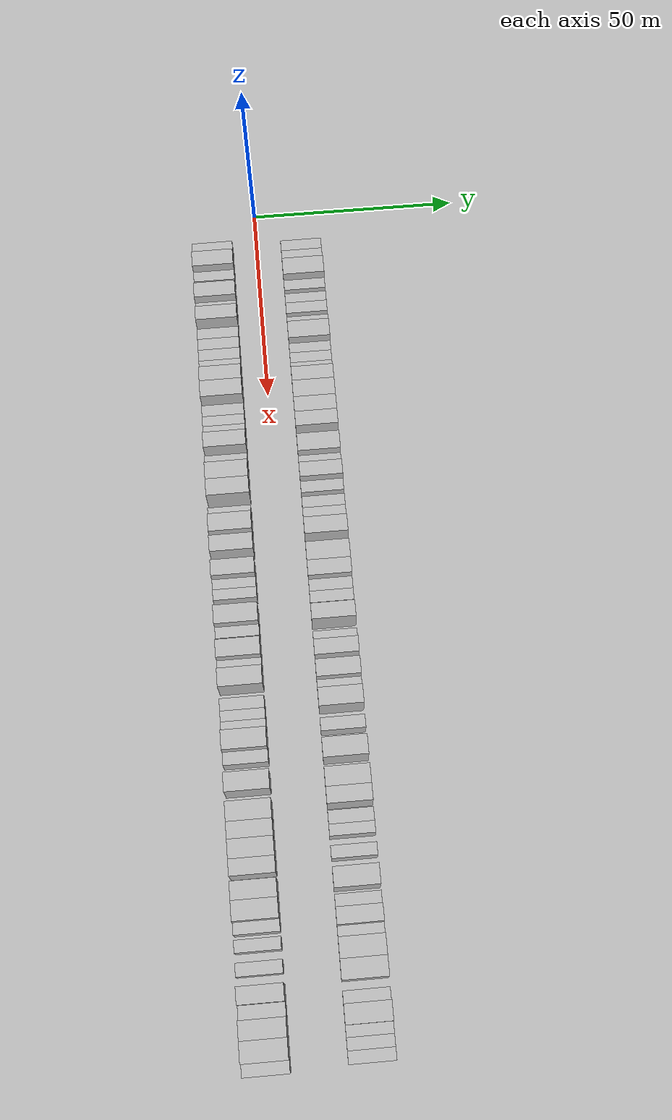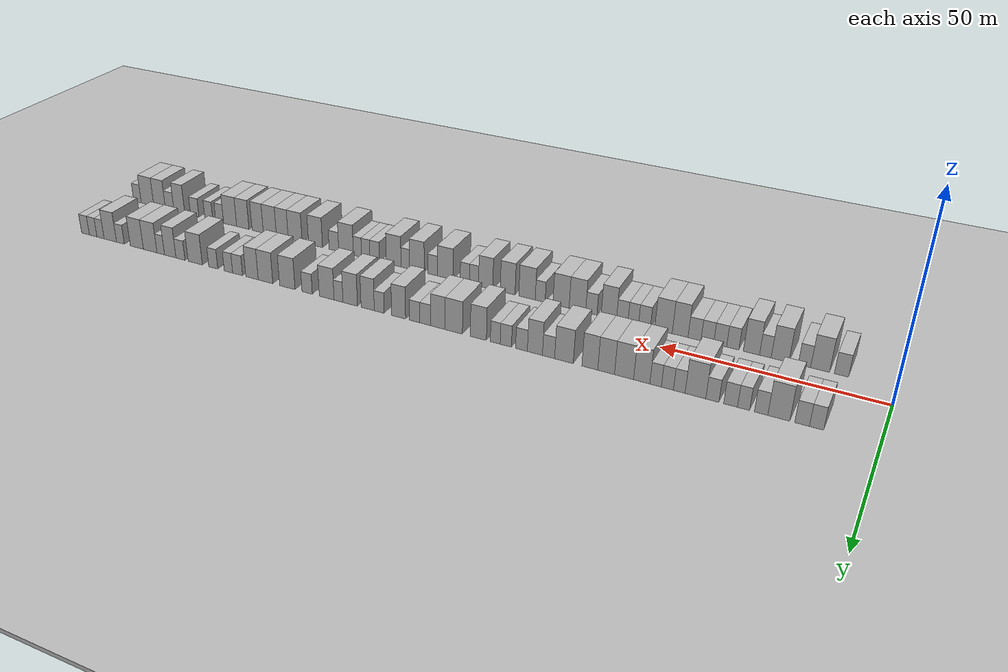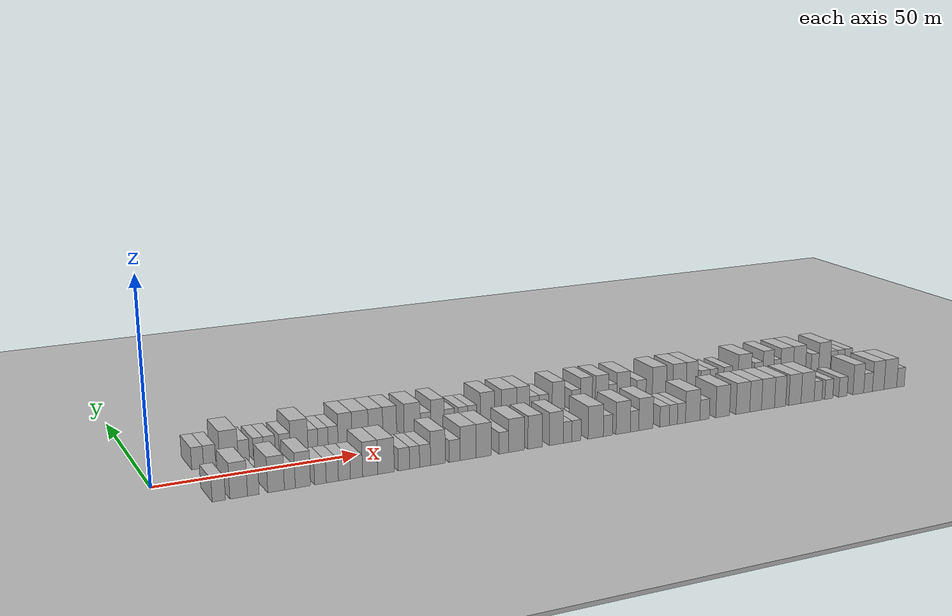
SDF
<?xml version="1.0" encoding="utf-8"?>

<sdf version="1.6">

   <world name="default">

      <gui fullscreen="0">

         <camera name="user_camera">

            <pose>-15 0 4.57585 0 0 0</pose>

            <view_controller>orbit</view_controller>

         </camera>

      </gui>

      <scene>

         <sky>

           <clouds>

             <speed>12</speed>

           </clouds>

         </sky>

         <ambient>0.4 0.4 0.4 1</ambient>

         <background>0.7 0.7 0.7 1</background>

         <shadows>1</shadows>

      </scene>

      <gravity>0 0 -9.8066</gravity>

      <magnetic_field>6e-06 2.3e-05 -4.2e-05</magnetic_field>

      <physics default="0" name="default_physics" type="ode">

         <ode>

            <solver>

               <type>quick</type>

               <iters>10</iters>

               <sor>1.0</sor>

               <use_dynamic_moi_rescaling>0</use_dynamic_moi_rescaling>

            </solver>

            <constraints>

               <cfm>0</cfm>

               <erp>0.2</erp>

               <contact_max_correcting_vel>100</contact_max_correcting_vel>

               <contact_surface_layer>0.001</contact_surface_layer>

            </constraints>

         </ode>

         <max_step_size>0.004</max_step_size>

         <real_time_factor>1</real_time_factor>

         <real_time_update_rate>250</real_time_update_rate>

      </physics>

      <light name="sun" type="directional">

         <cast_shadows>1</cast_shadows>

         <pose>0 0 10 0 0 0</pose>

         <diffuse>0.8 0.8 0.8 1</diffuse>

         <specular>0.2 0.2 0.2 1</specular>

         <attenuation>

            <range>1000</range>

            <constant>0.9</constant>

            <linear>0.01</linear>

            <quadratic>0.001</quadratic>

         </attenuation>

         <direction>-0.5 0.1 -0.9</direction>

      </light>

      <include>

         <name>ground_plane_1</name>

         <uri>model://HANNAS_ground_plane</uri>

         <pose>0 0 0  0 0 0</pose>

      </include>

      <include>

         <name>ground_plane_2</name>

         <uri>model://HANNAS_ground_plane</uri>

         <pose>100 0 0  0 0 0</pose>

      </include>

      <model name="building_1">

         <static>1</static>

         <pose frame="">12.4091 11.0000 0 0.000000 0.000000 1.570796</pose>

         <link name="link">

            <pose frame="">0 0 3.00 0 0 0</pose>

            <collision name="collision">

               <geometry>

                  <box>

                     <size>10.0000 2.8182 6.0000</size>

                  </box>

               </geometry>

               <max_contacts>10</max_contacts>

               <surface>

                  <contact>

                     <ode/>

                  </contact>

                  <bounce/>

                  <friction>

                     <torsional>

                        <ode/>

                     </torsional>

                     <ode/>

                  </friction>

               </surface>

            </collision>

            <visual name="visual">

               <cast_shadows>0</cast_shadows>

               <geometry>

                  <box>

                     <size>10.0000 2.8182 6.0000</size>

                  </box>

               </geometry>

               <material>

                  <script>

                     <uri>model://HANNAS_wall/materials/scripts</uri>

                     <uri>model://HANNAS_wall/materials/textures</uri>

                     <name>vrc/HANNAS_wall</name>

                  </script>

               </material>

            </visual>

            <self_collide>0</self_collide>

            <enable_wind>0</enable_wind>

            <kinematic>0</kinematic>

         </link>

      </model>

      <model name="building_2">

         <static>1</static>

         <pose frame="">15.2784 11.0000 0 0.000000 0.000000 1.570796</pose>

         <link name="link">

            <pose frame="">0 0 3.00 0 0 0</pose>

            <collision name="collision">

               <geometry>

                  <box>

                     <size>10.0000 2.9203 6.0000</size>

                  </box>

               </geometry>

               <max_contacts>10</max_contacts>

               <surface>

                  <contact>

                     <ode/>

                  </contact>

                  <bounce/>

                  <friction>

                     <torsional>

                        <ode/>

                     </torsional>

                     <ode/>

                  </friction>

               </surface>

            </collision>

            <visual name="visual">

               <cast_shadows>0</cast_shadows>

               <geometry>

                  <box>

                     <size>10.0000 2.9203 6.0000</size>

                  </box>

               </geometry>

               <material>

                  <script>

                     <uri>model://HANNAS_wall/materials/scripts</uri>

                     <uri>model://HANNAS_wall/materials/textures</uri>

                     <name>vrc/HANNAS_wall</name>

                  </script>

               </material>

            </visual>

            <self_collide>0</self_collide>

            <enable_wind>0</enable_wind>

            <kinematic>0</kinematic>

         </link>

      </model>

      <model name="building_3">

         <static>1</static>

         <pose frame="">19.9652 11.0000 0 0.000000 0.000000 1.570796</pose>

         <link name="link">

            <pose frame="">0 0 4.50 0 0 0</pose>

            <collision name="collision">

               <geometry>

                  <box>

                     <size>10.0000 4.4532 9.0000</size>

                  </box>

               </geometry>

               <max_contacts>10</max_contacts>

               <surface>

                  <contact>

                     <ode/>

                  </contact>

                  <bounce/>

                  <friction>

                     <torsional>

                        <ode/>

                     </torsional>

                     <ode/>

                  </friction>

               </surface>

            </collision>

            <visual name="visual">

               <cast_shadows>0</cast_shadows>

               <geometry>

                  <box>

                     <size>10.0000 4.4532 9.0000</size>

                  </box>

               </geometry>

               <material>

                  <script>

                     <uri>model://HANNAS_wall/materials/scripts</uri>

                     <uri>model://HANNAS_wall/materials/textures</uri>

                     <name>vrc/HANNAS_wall</name>

                  </script>

               </material>

            </visual>

            <self_collide>0</self_collide>

            <enable_wind>0</enable_wind>

            <kinematic>0</kinematic>

         </link>

      </model>

      <model name="building_4">

         <static>1</static>

         <pose frame="">23.5626 11.0000 0 0.000000 0.000000 1.570796</pose>

         <link name="link">

            <pose frame="">0 0 3.00 0 0 0</pose>

            <collision name="collision">

               <geometry>

                  <box>

                     <size>10.0000 2.7417 6.0000</size>

                  </box>

               </geometry>

               <max_contacts>10</max_contacts>

               <surface>

                  <contact>

                     <ode/>

                  </contact>

                  <bounce/>

                  <friction>

                     <torsional>

                        <ode/>

                     </torsional>

                     <ode/>

                  </friction>

               </surface>

            </collision>

            <visual name="visual">

               <cast_shadows>0</cast_shadows>

               <geometry>

                  <box>

                     <size>10.0000 2.7417 6.0000</size>

                  </box>

               </geometry>

               <material>

                  <script>

                     <uri>model://HANNAS_wall/materials/scripts</uri>

                     <uri>model://HANNAS_wall/materials/textures</uri>

                     <name>vrc/HANNAS_wall</name>

                  </script>

               </material>

            </visual>

            <self_collide>0</self_collide>

            <enable_wind>0</enable_wind>

            <kinematic>0</kinematic>

         </link>

      </model>

      <model name="building_5">

         <static>1</static>

         <pose frame="">27.1903 11.0000 0 0.000000 0.000000 1.570796</pose>

         <link name="link">

            <pose frame="">0 0 3.00 0 0 0</pose>

            <collision name="collision">

               <geometry>

                  <box>

                     <size>10.0000 2.5137 6.0000</size>

                  </box>

               </geometry>

               <max_contacts>10</max_contacts>

               <surface>

                  <contact>

                     <ode/>

                  </contact>

                  <bounce/>

                  <friction>

                     <torsional>

                        <ode/>

                     </torsional>

                     <ode/>

                  </friction>

               </surface>

            </collision>

            <visual name="visual">

               <cast_shadows>0</cast_shadows>

               <geometry>

                  <box>

                     <size>10.0000 2.5137 6.0000</size>

                  </box>

               </geometry>

               <material>

                  <script>

                     <uri>model://HANNAS_wall/materials/scripts</uri>

                     <uri>model://HANNAS_wall/materials/textures</uri>

                     <name>vrc/HANNAS_wall</name>

                  </script>

               </material>

            </visual>

            <self_collide>0</self_collide>

            <enable_wind>0</enable_wind>

            <kinematic>0</kinematic>

         </link>

      </model>

      <model name="building_6">

         <static>1</static>

         <pose frame="">29.8882 11.0000 0 0.000000 0.000000 1.570796</pose>

         <link name="link">

            <pose frame="">0 0 3.00 0 0 0</pose>

            <collision name="collision">

               <geometry>

                  <box>

                     <size>10.0000 2.8821 6.0000</size>

                  </box>

               </geometry>

               <max_contacts>10</max_contacts>

               <surface>

                  <contact>

                     <ode/>

                  </contact>

                  <bounce/>

                  <friction>

                     <torsional>

                        <ode/>

                     </torsional>

                     <ode/>

                  </friction>

               </surface>

            </collision>

            <visual name="visual">

               <cast_shadows>0</cast_shadows>

               <geometry>

                  <box>

                     <size>10.0000 2.8821 6.0000</size>

                  </box>

               </geometry>

               <material>

                  <script>

                     <uri>model://HANNAS_wall/materials/scripts</uri>

                     <uri>model://HANNAS_wall/materials/textures</uri>

                     <name>vrc/HANNAS_wall</name>

                  </script>

               </material>

            </visual>

            <self_collide>0</self_collide>

            <enable_wind>0</enable_wind>

            <kinematic>0</kinematic>

         </link>

      </model>

      <model name="building_7">

         <static>1</static>

         <pose frame="">33.7209 11.0000 0 0.000000 0.000000 1.570796</pose>

         <link name="link">

            <pose frame="">0 0 3.00 0 0 0</pose>

            <collision name="collision">

               <geometry>

                  <box>

                     <size>10.0000 2.7834 6.0000</size>

                  </box>

               </geometry>

               <max_contacts>10</max_contacts>

               <surface>

                  <contact>

                     <ode/>

                  </contact>

                  <bounce/>

                  <friction>

                     <torsional>

                        <ode/>

                     </torsional>

                     <ode/>

                  </friction>

               </surface>

            </collision>

            <visual name="visual">

               <cast_shadows>0</cast_shadows>

               <geometry>

                  <box>

                     <size>10.0000 2.7834 6.0000</size>

                  </box>

               </geometry>

               <material>

                  <script>

                     <uri>model://HANNAS_wall/materials/scripts</uri>

                     <uri>model://HANNAS_wall/materials/textures</uri>

                     <name>vrc/HANNAS_wall</name>

                  </script>

               </material>

            </visual>

            <self_collide>0</self_collide>

            <enable_wind>0</enable_wind>

            <kinematic>0</kinematic>

         </link>

      </model>

      <model name="building_8">

         <static>1</static>

         <pose frame="">37.3267 11.0000 0 0.000000 0.000000 1.570796</pose>

         <link name="link">

            <pose frame="">0 0 4.50 0 0 0</pose>

            <collision name="collision">

               <geometry>

                  <box>

                     <size>10.0000 4.4282 9.0000</size>

                  </box>

               </geometry>

               <max_contacts>10</max_contacts>

               <surface>

                  <contact>

                     <ode/>

                  </contact>

                  <bounce/>

                  <friction>

                     <torsional>

                        <ode/>

                     </torsional>

                     <ode/>

                  </friction>

               </surface>

            </collision>

            <visual name="visual">

               <cast_shadows>0</cast_shadows>

               <geometry>

                  <box>

                     <size>10.0000 4.4282 9.0000</size>

                  </box>

               </geometry>

               <material>

                  <script>

                     <uri>model://HANNAS_wall/materials/scripts</uri>

                     <uri>model://HANNAS_wall/materials/textures</uri>

                     <name>vrc/HANNAS_wall</name>

                  </script>

               </material>

            </visual>

            <self_collide>0</self_collide>

            <enable_wind>0</enable_wind>

            <kinematic>0</kinematic>

         </link>

      </model>

      <model name="building_9">

         <static>1</static>

         <pose frame="">40.8081 11.0000 0 0.000000 0.000000 1.570796</pose>

         <link name="link">

            <pose frame="">0 0 3.00 0 0 0</pose>

            <collision name="collision">

               <geometry>

                  <box>

                     <size>10.0000 2.5346 6.0000</size>

                  </box>

               </geometry>

               <max_contacts>10</max_contacts>

               <surface>

                  <contact>

                     <ode/>

                  </contact>

                  <bounce/>

                  <friction>

                     <torsional>

                        <ode/>

                     </torsional>

                     <ode/>

                  </friction>

               </surface>

            </collision>

            <visual name="visual">

               <cast_shadows>0</cast_shadows>

               <geometry>

                  <box>

                     <size>10.0000 2.5346 6.0000</size>

                  </box>

               </geometry>

               <material>

                  <script>

                     <uri>model://HANNAS_wall/materials/scripts</uri>

                     <uri>model://HANNAS_wall/materials/textures</uri>

                     <name>vrc/HANNAS_wall</name>

                  </script>

               </material>

            </visual>

            <self_collide>0</self_collide>

            <enable_wind>0</enable_wind>

            <kinematic>0</kinematic>

         </link>

      </model>

      <model name="building_10">

         <static>1</static>

         <pose frame="">43.3943 11.0000 0 0.000000 0.000000 1.570796</pose>

         <link name="link">

            <pose frame="">0 0 3.00 0 0 0</pose>

            <collision name="collision">

               <geometry>

                  <box>

                     <size>10.0000 2.6378 6.0000</size>

                  </box>

               </geometry>

               <max_contacts>10</max_contacts>

               <surface>

                  <contact>

                     <ode/>

                  </contact>

                  <bounce/>

                  <friction>

                     <torsional>

                        <ode/>

                     </torsional>

                     <ode/>

                  </friction>

               </surface>

            </collision>

            <visual name="visual">

               <cast_shadows>0</cast_shadows>

               <geometry>

                  <box>

                     <size>10.0000 2.6378 6.0000</size>

                  </box>

               </geometry>

               <material>

                  <script>

                     <uri>model://HANNAS_wall/materials/scripts</uri>

                     <uri>model://HANNAS_wall/materials/textures</uri>

                     <name>vrc/HANNAS_wall</name>

                  </script>

               </material>

            </visual>

            <self_collide>0</self_collide>

            <enable_wind>0</enable_wind>

            <kinematic>0</kinematic>

         </link>

      </model>

      <model name="building_11">

         <static>1</static>

         <pose frame="">45.9849 11.0000 0 0.000000 0.000000 1.570796</pose>

         <link name="link">

            <pose frame="">0 0 3.00 0 0 0</pose>

            <collision name="collision">

               <geometry>

                  <box>

                     <size>10.0000 2.5434 6.0000</size>

                  </box>

               </geometry>

               <max_contacts>10</max_contacts>

               <surface>

                  <contact>

                     <ode/>

                  </contact>

                  <bounce/>

                  <friction>

                     <torsional>

                        <ode/>

                     </torsional>

                     <ode/>

                  </friction>

               </surface>

            </collision>

            <visual name="visual">

               <cast_shadows>0</cast_shadows>

               <geometry>

                  <box>

                     <size>10.0000 2.5434 6.0000</size>

                  </box>

               </geometry>

               <material>

                  <script>

                     <uri>model://HANNAS_wall/materials/scripts</uri>

                     <uri>model://HANNAS_wall/materials/textures</uri>

                     <name>vrc/HANNAS_wall</name>

                  </script>

               </material>

            </visual>

            <self_collide>0</self_collide>

            <enable_wind>0</enable_wind>

            <kinematic>0</kinematic>

         </link>

      </model>

      <model name="building_12">

         <static>1</static>

         <pose frame="">49.0629 11.0000 0 0.000000 0.000000 1.570796</pose>

         <link name="link">

            <pose frame="">0 0 4.50 0 0 0</pose>

            <collision name="collision">

               <geometry>

                  <box>

                     <size>10.0000 3.6127 9.0000</size>

                  </box>

               </geometry>

               <max_contacts>10</max_contacts>

               <surface>

                  <contact>

                     <ode/>

                  </contact>

                  <bounce/>

                  <friction>

                     <torsional>

                        <ode/>

                     </torsional>

                     <ode/>

                  </friction>

               </surface>

            </collision>

            <visual name="visual">

               <cast_shadows>0</cast_shadows>

               <geometry>

                  <box>

                     <size>10.0000 3.6127 9.0000</size>

                  </box>

               </geometry>

               <material>

                  <script>

                     <uri>model://HANNAS_wall/materials/scripts</uri>

                     <uri>model://HANNAS_wall/materials/textures</uri>

                     <name>vrc/HANNAS_wall</name>

                  </script>

               </material>

            </visual>

            <self_collide>0</self_collide>

            <enable_wind>0</enable_wind>

            <kinematic>0</kinematic>

         </link>

      </model>

      <model name="building_13">

         <static>1</static>

         <pose frame="">53.0228 11.0000 0 0.000000 0.000000 1.570796</pose>

         <link name="link">

            <pose frame="">0 0 4.50 0 0 0</pose>

            <collision name="collision">

               <geometry>

                  <box>

                     <size>10.0000 4.3072 9.0000</size>

                  </box>

               </geometry>

               <max_contacts>10</max_contacts>

               <surface>

                  <contact>

                     <ode/>

                  </contact>

                  <bounce/>

                  <friction>

                     <torsional>

                        <ode/>

                     </torsional>

                     <ode/>

                  </friction>

               </surface>

            </collision>

            <visual name="visual">

               <cast_shadows>0</cast_shadows>

               <geometry>

                  <box>

                     <size>10.0000 4.3072 9.0000</size>

                  </box>

               </geometry>

               <material>

                  <script>

                     <uri>model://HANNAS_wall/materials/scripts</uri>

                     <uri>model://HANNAS_wall/materials/textures</uri>

                     <name>vrc/HANNAS_wall</name>

                  </script>

               </material>

            </visual>

            <self_collide>0</self_collide>

            <enable_wind>0</enable_wind>

            <kinematic>0</kinematic>

         </link>

      </model>

      <model name="building_14">

         <static>1</static>

         <pose frame="">57.0884 11.0000 0 0.000000 0.000000 1.570796</pose>

         <link name="link">

            <pose frame="">0 0 4.50 0 0 0</pose>

            <collision name="collision">

               <geometry>

                  <box>

                     <size>10.0000 3.8240 9.0000</size>

                  </box>

               </geometry>

               <max_contacts>10</max_contacts>

               <surface>

                  <contact>

                     <ode/>

                  </contact>

                  <bounce/>

                  <friction>

                     <torsional>

                        <ode/>

                     </torsional>

                     <ode/>

                  </friction>

               </surface>

            </collision>

            <visual name="visual">

               <cast_shadows>0</cast_shadows>

               <geometry>

                  <box>

                     <size>10.0000 3.8240 9.0000</size>

                  </box>

               </geometry>

               <material>

                  <script>

                     <uri>model://HANNAS_wall/materials/scripts</uri>

                     <uri>model://HANNAS_wall/materials/textures</uri>

                     <name>vrc/HANNAS_wall</name>

                  </script>

               </material>

            </visual>

            <self_collide>0</self_collide>

            <enable_wind>0</enable_wind>

            <kinematic>0</kinematic>

         </link>

      </model>

      <model name="building_15">

         <static>1</static>

         <pose frame="">60.8358 11.0000 0 0.000000 0.000000 1.570796</pose>

         <link name="link">

            <pose frame="">0 0 4.50 0 0 0</pose>

            <collision name="collision">

               <geometry>

                  <box>

                     <size>10.0000 3.6707 9.0000</size>

                  </box>

               </geometry>

               <max_contacts>10</max_contacts>

               <surface>

                  <contact>

                     <ode/>

                  </contact>

                  <bounce/>

                  <friction>

                     <torsional>

                        <ode/>

                     </torsional>

                     <ode/>

                  </friction>

               </surface>

            </collision>

            <visual name="visual">

               <cast_shadows>0</cast_shadows>

               <geometry>

                  <box>

                     <size>10.0000 3.6707 9.0000</size>

                  </box>

               </geometry>

               <material>

                  <script>

                     <uri>model://HANNAS_wall/materials/scripts</uri>

                     <uri>model://HANNAS_wall/materials/textures</uri>

                     <name>vrc/HANNAS_wall</name>

                  </script>

               </material>

            </visual>

            <self_collide>0</self_collide>

            <enable_wind>0</enable_wind>

            <kinematic>0</kinematic>

         </link>

      </model>

      <model name="building_16">

         <static>1</static>

         <pose frame="">66.8701 11.0000 0 0.000000 0.000000 1.570796</pose>

         <link name="link">

            <pose frame="">0 0 4.50 0 0 0</pose>

            <collision name="collision">

               <geometry>

                  <box>

                     <size>10.0000 4.3979 9.0000</size>

                  </box>

               </geometry>

               <max_contacts>10</max_contacts>

               <surface>

                  <contact>

                     <ode/>

                  </contact>

                  <bounce/>

                  <friction>

                     <torsional>

                        <ode/>

                     </torsional>

                     <ode/>

                  </friction>

               </surface>

            </collision>

            <visual name="visual">

               <cast_shadows>0</cast_shadows>

               <geometry>

                  <box>

                     <size>10.0000 4.3979 9.0000</size>

                  </box>

               </geometry>

               <material>

                  <script>

                     <uri>model://HANNAS_wall/materials/scripts</uri>

                     <uri>model://HANNAS_wall/materials/textures</uri>

                     <name>vrc/HANNAS_wall</name>

                  </script>

               </material>

            </visual>

            <self_collide>0</self_collide>

            <enable_wind>0</enable_wind>

            <kinematic>0</kinematic>

         </link>

      </model>

      <model name="building_17">

         <static>1</static>

         <pose frame="">70.5187 11.0000 0 0.000000 0.000000 1.570796</pose>

         <link name="link">

            <pose frame="">0 0 3.00 0 0 0</pose>

            <collision name="collision">

               <geometry>

                  <box>

                     <size>10.0000 2.8995 6.0000</size>

                  </box>

               </geometry>

               <max_contacts>10</max_contacts>

               <surface>

                  <contact>

                     <ode/>

                  </contact>

                  <bounce/>

                  <friction>

                     <torsional>

                        <ode/>

                     </torsional>

                     <ode/>

                  </friction>

               </surface>

            </collision>

            <visual name="visual">

               <cast_shadows>0</cast_shadows>

               <geometry>

                  <box>

                     <size>10.0000 2.8995 6.0000</size>

                  </box>

               </geometry>

               <material>

                  <script>

                     <uri>model://HANNAS_wall/materials/scripts</uri>

                     <uri>model://HANNAS_wall/materials/textures</uri>

                     <name>vrc/HANNAS_wall</name>

                  </script>

               </material>

            </visual>

            <self_collide>0</self_collide>

            <enable_wind>0</enable_wind>

            <kinematic>0</kinematic>

         </link>

      </model>

      <model name="building_18">

         <static>1</static>

         <pose frame="">73.7836 11.0000 0 0.000000 0.000000 1.570796</pose>

         <link name="link">

            <pose frame="">0 0 4.50 0 0 0</pose>

            <collision name="collision">

               <geometry>

                  <box>

                     <size>10.0000 3.6303 9.0000</size>

                  </box>

               </geometry>

               <max_contacts>10</max_contacts>

               <surface>

                  <contact>

                     <ode/>

                  </contact>

                  <bounce/>

                  <friction>

                     <torsional>

                        <ode/>

                     </torsional>

                     <ode/>

                  </friction>

               </surface>

            </collision>

            <visual name="visual">

               <cast_shadows>0</cast_shadows>

               <geometry>

                  <box>

                     <size>10.0000 3.6303 9.0000</size>

                  </box>

               </geometry>

               <material>

                  <script>

                     <uri>model://HANNAS_wall/materials/scripts</uri>

                     <uri>model://HANNAS_wall/materials/textures</uri>

                     <name>vrc/HANNAS_wall</name>

                  </script>

               </material>

            </visual>

            <self_collide>0</self_collide>

            <enable_wind>0</enable_wind>

            <kinematic>0</kinematic>

         </link>

      </model>

      <model name="building_19">

         <static>1</static>

         <pose frame="">77.0267 11.0000 0 0.000000 0.000000 1.570796</pose>

         <link name="link">

            <pose frame="">0 0 3.00 0 0 0</pose>

            <collision name="collision">

               <geometry>

                  <box>

                     <size>10.0000 2.8559 6.0000</size>

                  </box>

               </geometry>

               <max_contacts>10</max_contacts>

               <surface>

                  <contact>

                     <ode/>

                  </contact>

                  <bounce/>

                  <friction>

                     <torsional>

                        <ode/>

                     </torsional>

                     <ode/>

                  </friction>

               </surface>

            </collision>

            <visual name="visual">

               <cast_shadows>0</cast_shadows>

               <geometry>

                  <box>

                     <size>10.0000 2.8559 6.0000</size>

                  </box>

               </geometry>

               <material>

                  <script>

                     <uri>model://HANNAS_wall/materials/scripts</uri>

                     <uri>model://HANNAS_wall/materials/textures</uri>

                     <name>vrc/HANNAS_wall</name>

                  </script>

               </material>

            </visual>

            <self_collide>0</self_collide>

            <enable_wind>0</enable_wind>

            <kinematic>0</kinematic>

         </link>

      </model>

      <model name="building_20">

         <static>1</static>

         <pose frame="">80.8412 11.0000 0 0.000000 0.000000 1.570796</pose>

         <link name="link">

            <pose frame="">0 0 3.00 0 0 0</pose>

            <collision name="collision">

               <geometry>

                  <box>

                     <size>10.0000 2.7729 6.0000</size>

                  </box>

               </geometry>

               <max_contacts>10</max_contacts>

               <surface>

                  <contact>

                     <ode/>

                  </contact>

                  <bounce/>

                  <friction>

                     <torsional>

                        <ode/>

                     </torsional>

                     <ode/>

                  </friction>

               </surface>

            </collision>

            <visual name="visual">

               <cast_shadows>0</cast_shadows>

               <geometry>

                  <box>

                     <size>10.0000 2.7729 6.0000</size>

                  </box>

               </geometry>

               <material>

                  <script>

                     <uri>model://HANNAS_wall/materials/scripts</uri>

                     <uri>model://HANNAS_wall/materials/textures</uri>

                     <name>vrc/HANNAS_wall</name>

                  </script>

               </material>

            </visual>

            <self_collide>0</self_collide>

            <enable_wind>0</enable_wind>

            <kinematic>0</kinematic>

         </link>

      </model>

      <model name="building_21">

         <static>1</static>

         <pose frame="">83.4422 11.0000 0 0.000000 0.000000 1.570796</pose>

         <link name="link">

            <pose frame="">0 0 3.00 0 0 0</pose>

            <collision name="collision">

               <geometry>

                  <box>

                     <size>10.0000 2.4292 6.0000</size>

                  </box>

               </geometry>

               <max_contacts>10</max_contacts>

               <surface>

                  <contact>

                     <ode/>

                  </contact>

                  <bounce/>

                  <friction>

                     <torsional>

                        <ode/>

                     </torsional>

                     <ode/>

                  </friction>

               </surface>

            </collision>

            <visual name="visual">

               <cast_shadows>0</cast_shadows>

               <geometry>

                  <box>

                     <size>10.0000 2.4292 6.0000</size>

                  </box>

               </geometry>

               <material>

                  <script>

                     <uri>model://HANNAS_wall/materials/scripts</uri>

                     <uri>model://HANNAS_wall/materials/textures</uri>

                     <name>vrc/HANNAS_wall</name>

                  </script>

               </material>

            </visual>

            <self_collide>0</self_collide>

            <enable_wind>0</enable_wind>

            <kinematic>0</kinematic>

         </link>

      </model>

      <model name="building_22">

         <static>1</static>

         <pose frame="">87.6706 11.0000 0 0.000000 0.000000 1.570796</pose>

         <link name="link">

            <pose frame="">0 0 4.50 0 0 0</pose>

            <collision name="collision">

               <geometry>

                  <box>

                     <size>10.0000 4.0277 9.0000</size>

                  </box>

               </geometry>

               <max_contacts>10</max_contacts>

               <surface>

                  <contact>

                     <ode/>

                  </contact>

                  <bounce/>

                  <friction>

                     <torsional>

                        <ode/>

                     </torsional>

                     <ode/>

                  </friction>

               </surface>

            </collision>

            <visual name="visual">

               <cast_shadows>0</cast_shadows>

               <geometry>

                  <box>

                     <size>10.0000 4.0277 9.0000</size>

                  </box>

               </geometry>

               <material>

                  <script>

                     <uri>model://HANNAS_wall/materials/scripts</uri>

                     <uri>model://HANNAS_wall/materials/textures</uri>

                     <name>vrc/HANNAS_wall</name>

                  </script>

               </material>

            </visual>

            <self_collide>0</self_collide>

            <enable_wind>0</enable_wind>

            <kinematic>0</kinematic>

         </link>

      </model>

      <model name="building_23">

         <static>1</static>

         <pose frame="">93.8970 11.0000 0 0.000000 0.000000 1.570796</pose>

         <link name="link">

            <pose frame="">0 0 4.50 0 0 0</pose>

            <collision name="collision">

               <geometry>

                  <box>

                     <size>10.0000 4.4251 9.0000</size>

                  </box>

               </geometry>

               <max_contacts>10</max_contacts>

               <surface>

                  <contact>

                     <ode/>

                  </contact>

                  <bounce/>

                  <friction>

                     <torsional>

                        <ode/>

                     </torsional>

                     <ode/>

                  </friction>

               </surface>

            </collision>

            <visual name="visual">

               <cast_shadows>0</cast_shadows>

               <geometry>

                  <box>

                     <size>10.0000 4.4251 9.0000</size>

                  </box>

               </geometry>

               <material>

                  <script>

                     <uri>model://HANNAS_wall/materials/scripts</uri>

                     <uri>model://HANNAS_wall/materials/textures</uri>

                     <name>vrc/HANNAS_wall</name>

                  </script>

               </material>

            </visual>

            <self_collide>0</self_collide>

            <enable_wind>0</enable_wind>

            <kinematic>0</kinematic>

         </link>

      </model>

      <model name="building_24">

         <static>1</static>

         <pose frame="">97.9638 11.0000 0 0.000000 0.000000 1.570796</pose>

         <link name="link">

            <pose frame="">0 0 4.50 0 0 0</pose>

            <collision name="collision">

               <geometry>

                  <box>

                     <size>10.0000 3.7085 9.0000</size>

                  </box>

               </geometry>

               <max_contacts>10</max_contacts>

               <surface>

                  <contact>

                     <ode/>

                  </contact>

                  <bounce/>

                  <friction>

                     <torsional>

                        <ode/>

                     </torsional>

                     <ode/>

                  </friction>

               </surface>

            </collision>

            <visual name="visual">

               <cast_shadows>0</cast_shadows>

               <geometry>

                  <box>

                     <size>10.0000 3.7085 9.0000</size>

                  </box>

               </geometry>

               <material>

                  <script>

                     <uri>model://HANNAS_wall/materials/scripts</uri>

                     <uri>model://HANNAS_wall/materials/textures</uri>

                     <name>vrc/HANNAS_wall</name>

                  </script>

               </material>

            </visual>

            <self_collide>0</self_collide>

            <enable_wind>0</enable_wind>

            <kinematic>0</kinematic>

         </link>

      </model>

      <model name="building_25">

         <static>1</static>

         <pose frame="">101.2395 11.0000 0 0.000000 0.000000 1.570796</pose>

         <link name="link">

            <pose frame="">0 0 3.00 0 0 0</pose>

            <collision name="collision">

               <geometry>

                  <box>

                     <size>10.0000 2.8429 6.0000</size>

                  </box>

               </geometry>

               <max_contacts>10</max_contacts>

               <surface>

                  <contact>

                     <ode/>

                  </contact>

                  <bounce/>

                  <friction>

                     <torsional>

                        <ode/>

                     </torsional>

                     <ode/>

                  </friction>

               </surface>

            </collision>

            <visual name="visual">

               <cast_shadows>0</cast_shadows>

               <geometry>

                  <box>

                     <size>10.0000 2.8429 6.0000</size>

                  </box>

               </geometry>

               <material>

                  <script>

                     <uri>model://HANNAS_wall/materials/scripts</uri>

                     <uri>model://HANNAS_wall/materials/textures</uri>

                     <name>vrc/HANNAS_wall</name>

                  </script>

               </material>

            </visual>

            <self_collide>0</self_collide>

            <enable_wind>0</enable_wind>

            <kinematic>0</kinematic>

         </link>

      </model>

      <model name="building_26">

         <static>1</static>

         <pose frame="">104.0441 11.0000 0 0.000000 0.000000 1.570796</pose>

         <link name="link">

            <pose frame="">0 0 3.00 0 0 0</pose>

            <collision name="collision">

               <geometry>

                  <box>

                     <size>10.0000 2.7664 6.0000</size>

                  </box>

               </geometry>

               <max_contacts>10</max_contacts>

               <surface>

                  <contact>

                     <ode/>

                  </contact>

                  <bounce/>

                  <friction>

                     <torsional>

                        <ode/>

                     </torsional>

                     <ode/>

                  </friction>

               </surface>

            </collision>

            <visual name="visual">

               <cast_shadows>0</cast_shadows>

               <geometry>

                  <box>

                     <size>10.0000 2.7664 6.0000</size>

                  </box>

               </geometry>

               <material>

                  <script>

                     <uri>model://HANNAS_wall/materials/scripts</uri>

                     <uri>model://HANNAS_wall/materials/textures</uri>

                     <name>vrc/HANNAS_wall</name>

                  </script>

               </material>

            </visual>

            <self_collide>0</self_collide>

            <enable_wind>0</enable_wind>

            <kinematic>0</kinematic>

         </link>

      </model>

      <model name="building_27">

         <static>1</static>

         <pose frame="">108.2860 11.0000 0 0.000000 0.000000 1.570796</pose>

         <link name="link">

            <pose frame="">0 0 4.50 0 0 0</pose>

            <collision name="collision">

               <geometry>

                  <box>

                     <size>10.0000 3.7175 9.0000</size>

                  </box>

               </geometry>

               <max_contacts>10</max_contacts>

               <surface>

                  <contact>

                     <ode/>

                  </contact>

                  <bounce/>

                  <friction>

                     <torsional>

                        <ode/>

                     </torsional>

                     <ode/>

                  </friction>

               </surface>

            </collision>

            <visual name="visual">

               <cast_shadows>0</cast_shadows>

               <geometry>

                  <box>

                     <size>10.0000 3.7175 9.0000</size>

                  </box>

               </geometry>

               <material>

                  <script>

                     <uri>model://HANNAS_wall/materials/scripts</uri>

                     <uri>model://HANNAS_wall/materials/textures</uri>

                     <name>vrc/HANNAS_wall</name>

                  </script>

               </material>

            </visual>

            <self_collide>0</self_collide>

            <enable_wind>0</enable_wind>

            <kinematic>0</kinematic>

         </link>

      </model>

      <model name="building_28">

         <static>1</static>

         <pose frame="">113.4828 11.0000 0 0.000000 0.000000 1.570796</pose>

         <link name="link">

            <pose frame="">0 0 3.00 0 0 0</pose>

            <collision name="collision">

               <geometry>

                  <box>

                     <size>10.0000 2.6761 6.0000</size>

                  </box>

               </geometry>

               <max_contacts>10</max_contacts>

               <surface>

                  <contact>

                     <ode/>

                  </contact>

                  <bounce/>

                  <friction>

                     <torsional>

                        <ode/>

                     </torsional>

                     <ode/>

                  </friction>

               </surface>

            </collision>

            <visual name="visual">

               <cast_shadows>0</cast_shadows>

               <geometry>

                  <box>

                     <size>10.0000 2.6761 6.0000</size>

                  </box>

               </geometry>

               <material>

                  <script>

                     <uri>model://HANNAS_wall/materials/scripts</uri>

                     <uri>model://HANNAS_wall/materials/textures</uri>

                     <name>vrc/HANNAS_wall</name>

                  </script>

               </material>

            </visual>

            <self_collide>0</self_collide>

            <enable_wind>0</enable_wind>

            <kinematic>0</kinematic>

         </link>

      </model>

      <model name="building_29">

         <static>1</static>

         <pose frame="">116.6218 11.0000 0 0.000000 0.000000 1.570796</pose>

         <link name="link">

            <pose frame="">0 0 4.50 0 0 0</pose>

            <collision name="collision">

               <geometry>

                  <box>

                     <size>10.0000 3.6017 9.0000</size>

                  </box>

               </geometry>

               <max_contacts>10</max_contacts>

               <surface>

                  <contact>

                     <ode/>

                  </contact>

                  <bounce/>

                  <friction>

                     <torsional>

                        <ode/>

                     </torsional>

                     <ode/>

                  </friction>

               </surface>

            </collision>

            <visual name="visual">

               <cast_shadows>0</cast_shadows>

               <geometry>

                  <box>

                     <size>10.0000 3.6017 9.0000</size>

                  </box>

               </geometry>

               <material>

                  <script>

                     <uri>model://HANNAS_wall/materials/scripts</uri>

                     <uri>model://HANNAS_wall/materials/textures</uri>

                     <name>vrc/HANNAS_wall</name>

                  </script>

               </material>

            </visual>

            <self_collide>0</self_collide>

            <enable_wind>0</enable_wind>

            <kinematic>0</kinematic>

         </link>

      </model>

      <model name="building_30">

         <static>1</static>

         <pose frame="">121.4236 11.0000 0 0.000000 0.000000 1.570796</pose>

         <link name="link">

            <pose frame="">0 0 4.50 0 0 0</pose>

            <collision name="collision">

               <geometry>

                  <box>

                     <size>10.0000 4.0019 9.0000</size>

                  </box>

               </geometry>

               <max_contacts>10</max_contacts>

               <surface>

                  <contact>

                     <ode/>

                  </contact>

                  <bounce/>

                  <friction>

                     <torsional>

                        <ode/>

                     </torsional>

                     <ode/>

                  </friction>

               </surface>

            </collision>

            <visual name="visual">

               <cast_shadows>0</cast_shadows>

               <geometry>

                  <box>

                     <size>10.0000 4.0019 9.0000</size>

                  </box>

               </geometry>

               <material>

                  <script>

                     <uri>model://HANNAS_wall/materials/scripts</uri>

                     <uri>model://HANNAS_wall/materials/textures</uri>

                     <name>vrc/HANNAS_wall</name>

                  </script>

               </material>

            </visual>

            <self_collide>0</self_collide>

            <enable_wind>0</enable_wind>

            <kinematic>0</kinematic>

         </link>

      </model>

      <model name="building_31">

         <static>1</static>

         <pose frame="">124.6648 11.0000 0 0.000000 0.000000 1.570796</pose>

         <link name="link">

            <pose frame="">0 0 3.00 0 0 0</pose>

            <collision name="collision">

               <geometry>

                  <box>

                     <size>10.0000 2.4805 6.0000</size>

                  </box>

               </geometry>

               <max_contacts>10</max_contacts>

               <surface>

                  <contact>

                     <ode/>

                  </contact>

                  <bounce/>

                  <friction>

                     <torsional>

                        <ode/>

                     </torsional>

                     <ode/>

                  </friction>

               </surface>

            </collision>

            <visual name="visual">

               <cast_shadows>0</cast_shadows>

               <geometry>

                  <box>

                     <size>10.0000 2.4805 6.0000</size>

                  </box>

               </geometry>

               <material>

                  <script>

                     <uri>model://HANNAS_wall/materials/scripts</uri>

                     <uri>model://HANNAS_wall/materials/textures</uri>

                     <name>vrc/HANNAS_wall</name>

                  </script>

               </material>

            </visual>

            <self_collide>0</self_collide>

            <enable_wind>0</enable_wind>

            <kinematic>0</kinematic>

         </link>

      </model>

      <model name="building_32">

         <static>1</static>

         <pose frame="">127.9962 11.0000 0 0.000000 0.000000 1.570796</pose>

         <link name="link">

            <pose frame="">0 0 4.50 0 0 0</pose>

            <collision name="collision">

               <geometry>

                  <box>

                     <size>10.0000 4.1823 9.0000</size>

                  </box>

               </geometry>

               <max_contacts>10</max_contacts>

               <surface>

                  <contact>

                     <ode/>

                  </contact>

                  <bounce/>

                  <friction>

                     <torsional>

                        <ode/>

                     </torsional>

                     <ode/>

                  </friction>

               </surface>

            </collision>

            <visual name="visual">

               <cast_shadows>0</cast_shadows>

               <geometry>

                  <box>

                     <size>10.0000 4.1823 9.0000</size>

                  </box>

               </geometry>

               <material>

                  <script>

                     <uri>model://HANNAS_wall/materials/scripts</uri>

                     <uri>model://HANNAS_wall/materials/textures</uri>

                     <name>vrc/HANNAS_wall</name>

                  </script>

               </material>

            </visual>

            <self_collide>0</self_collide>

            <enable_wind>0</enable_wind>

            <kinematic>0</kinematic>

         </link>

      </model>

      <model name="building_33">

         <static>1</static>

         <pose frame="">133.5678 11.0000 0 0.000000 0.000000 1.570796</pose>

         <link name="link">

            <pose frame="">0 0 3.00 0 0 0</pose>

            <collision name="collision">

               <geometry>

                  <box>

                     <size>10.0000 2.9610 6.0000</size>

                  </box>

               </geometry>

               <max_contacts>10</max_contacts>

               <surface>

                  <contact>

                     <ode/>

                  </contact>

                  <bounce/>

                  <friction>

                     <torsional>

                        <ode/>

                     </torsional>

                     <ode/>

                  </friction>

               </surface>

            </collision>

            <visual name="visual">

               <cast_shadows>0</cast_shadows>

               <geometry>

                  <box>

                     <size>10.0000 2.9610 6.0000</size>

                  </box>

               </geometry>

               <material>

                  <script>

                     <uri>model://HANNAS_wall/materials/scripts</uri>

                     <uri>model://HANNAS_wall/materials/textures</uri>

                     <name>vrc/HANNAS_wall</name>

                  </script>

               </material>

            </visual>

            <self_collide>0</self_collide>

            <enable_wind>0</enable_wind>

            <kinematic>0</kinematic>

         </link>

      </model>

      <model name="building_34">

         <static>1</static>

         <pose frame="">139.2877 11.0000 0 0.000000 0.000000 1.570796</pose>

         <link name="link">

            <pose frame="">0 0 4.50 0 0 0</pose>

            <collision name="collision">

               <geometry>

                  <box>

                     <size>10.0000 4.4787 9.0000</size>

                  </box>

               </geometry>

               <max_contacts>10</max_contacts>

               <surface>

                  <contact>

                     <ode/>

                  </contact>

                  <bounce/>

                  <friction>

                     <torsional>

                        <ode/>

                     </torsional>

                     <ode/>

                  </friction>

               </surface>

            </collision>

            <visual name="visual">

               <cast_shadows>0</cast_shadows>

               <geometry>

                  <box>

                     <size>10.0000 4.4787 9.0000</size>

                  </box>

               </geometry>

               <material>

                  <script>

                     <uri>model://HANNAS_wall/materials/scripts</uri>

                     <uri>model://HANNAS_wall/materials/textures</uri>

                     <name>vrc/HANNAS_wall</name>

                  </script>

               </material>

            </visual>

            <self_collide>0</self_collide>

            <enable_wind>0</enable_wind>

            <kinematic>0</kinematic>

         </link>

      </model>

      <model name="building_35">

         <static>1</static>

         <pose frame="">145.7002 11.0000 0 0.000000 0.000000 1.570796</pose>

         <link name="link">

            <pose frame="">0 0 4.50 0 0 0</pose>

            <collision name="collision">

               <geometry>

                  <box>

                     <size>10.0000 4.3463 9.0000</size>

                  </box>

               </geometry>

               <max_contacts>10</max_contacts>

               <surface>

                  <contact>

                     <ode/>

                  </contact>

                  <bounce/>

                  <friction>

                     <torsional>

                        <ode/>

                     </torsional>

                     <ode/>

                  </friction>

               </surface>

            </collision>

            <visual name="visual">

               <cast_shadows>0</cast_shadows>

               <geometry>

                  <box>

                     <size>10.0000 4.3463 9.0000</size>

                  </box>

               </geometry>

               <material>

                  <script>

                     <uri>model://HANNAS_wall/materials/scripts</uri>

                     <uri>model://HANNAS_wall/materials/textures</uri>

                     <name>vrc/HANNAS_wall</name>

                  </script>

               </material>

            </visual>

            <self_collide>0</self_collide>

            <enable_wind>0</enable_wind>

            <kinematic>0</kinematic>

         </link>

      </model>

      <model name="building_36">

         <static>1</static>

         <pose frame="">149.7222 11.0000 0 0.000000 0.000000 1.570796</pose>

         <link name="link">

            <pose frame="">0 0 4.50 0 0 0</pose>

            <collision name="collision">

               <geometry>

                  <box>

                     <size>10.0000 3.6979 9.0000</size>

                  </box>

               </geometry>

               <max_contacts>10</max_contacts>

               <surface>

                  <contact>

                     <ode/>

                  </contact>

                  <bounce/>

                  <friction>

                     <torsional>

                        <ode/>

                     </torsional>

                     <ode/>

                  </friction>

               </surface>

            </collision>

            <visual name="visual">

               <cast_shadows>0</cast_shadows>

               <geometry>

                  <box>

                     <size>10.0000 3.6979 9.0000</size>

                  </box>

               </geometry>

               <material>

                  <script>

                     <uri>model://HANNAS_wall/materials/scripts</uri>

                     <uri>model://HANNAS_wall/materials/textures</uri>

                     <name>vrc/HANNAS_wall</name>

                  </script>

               </material>

            </visual>

            <self_collide>0</self_collide>

            <enable_wind>0</enable_wind>

            <kinematic>0</kinematic>

         </link>

      </model>

      <model name="building_37">

         <static>1</static>

         <pose frame="">154.0695 11.0000 0 0.000000 0.000000 1.570796</pose>

         <link name="link">

            <pose frame="">0 0 3.00 0 0 0</pose>

            <collision name="collision">

               <geometry>

                  <box>

                     <size>10.0000 2.9967 6.0000</size>

                  </box>

               </geometry>

               <max_contacts>10</max_contacts>

               <surface>

                  <contact>

                     <ode/>

                  </contact>

                  <bounce/>

                  <friction>

                     <torsional>

                        <ode/>

                     </torsional>

                     <ode/>

                  </friction>

               </surface>

            </collision>

            <visual name="visual">

               <cast_shadows>0</cast_shadows>

               <geometry>

                  <box>

                     <size>10.0000 2.9967 6.0000</size>

                  </box>

               </geometry>

               <material>

                  <script>

                     <uri>model://HANNAS_wall/materials/scripts</uri>

                     <uri>model://HANNAS_wall/materials/textures</uri>

                     <name>vrc/HANNAS_wall</name>

                  </script>

               </material>

            </visual>

            <self_collide>0</self_collide>

            <enable_wind>0</enable_wind>

            <kinematic>0</kinematic>

         </link>

      </model>

      <model name="building_38">

         <static>1</static>

         <pose frame="">156.8507 11.0000 0 0.000000 0.000000 1.570796</pose>

         <link name="link">

            <pose frame="">0 0 3.00 0 0 0</pose>

            <collision name="collision">

               <geometry>

                  <box>

                     <size>10.0000 2.5656 6.0000</size>

                  </box>

               </geometry>

               <max_contacts>10</max_contacts>

               <surface>

                  <contact>

                     <ode/>

                  </contact>

                  <bounce/>

                  <friction>

                     <torsional>

                        <ode/>

                     </torsional>

                     <ode/>

                  </friction>

               </surface>

            </collision>

            <visual name="visual">

               <cast_shadows>0</cast_shadows>

               <geometry>

                  <box>

                     <size>10.0000 2.5656 6.0000</size>

                  </box>

               </geometry>

               <material>

                  <script>

                     <uri>model://HANNAS_wall/materials/scripts</uri>

                     <uri>model://HANNAS_wall/materials/textures</uri>

                     <name>vrc/HANNAS_wall</name>

                  </script>

               </material>

            </visual>

            <self_collide>0</self_collide>

            <enable_wind>0</enable_wind>

            <kinematic>0</kinematic>

         </link>

      </model>

      <model name="building_39">

         <static>1</static>

         <pose frame="">161.5285 11.0000 0 0.000000 0.000000 1.570796</pose>

         <link name="link">

            <pose frame="">0 0 3.00 0 0 0</pose>

            <collision name="collision">

               <geometry>

                  <box>

                     <size>10.0000 2.7900 6.0000</size>

                  </box>

               </geometry>

               <max_contacts>10</max_contacts>

               <surface>

                  <contact>

                     <ode/>

                  </contact>

                  <bounce/>

                  <friction>

                     <torsional>

                        <ode/>

                     </torsional>

                     <ode/>

                  </friction>

               </surface>

            </collision>

            <visual name="visual">

               <cast_shadows>0</cast_shadows>

               <geometry>

                  <box>

                     <size>10.0000 2.7900 6.0000</size>

                  </box>

               </geometry>

               <material>

                  <script>

                     <uri>model://HANNAS_wall/materials/scripts</uri>

                     <uri>model://HANNAS_wall/materials/textures</uri>

                     <name>vrc/HANNAS_wall</name>

                  </script>

               </material>

            </visual>

            <self_collide>0</self_collide>

            <enable_wind>0</enable_wind>

            <kinematic>0</kinematic>

         </link>

      </model>

      <model name="building_40">

         <static>1</static>

         <pose frame="">167.1482 11.0000 0 0.000000 0.000000 1.570796</pose>

         <link name="link">

            <pose frame="">0 0 4.50 0 0 0</pose>

            <collision name="collision">

               <geometry>

                  <box>

                     <size>10.0000 4.4494 9.0000</size>

                  </box>

               </geometry>

               <max_contacts>10</max_contacts>

               <surface>

                  <contact>

                     <ode/>

                  </contact>

                  <bounce/>

                  <friction>

                     <torsional>

                        <ode/>

                     </torsional>

                     <ode/>

                  </friction>

               </surface>

            </collision>

            <visual name="visual">

               <cast_shadows>0</cast_shadows>

               <geometry>

                  <box>

                     <size>10.0000 4.4494 9.0000</size>

                  </box>

               </geometry>

               <material>

                  <script>

                     <uri>model://HANNAS_wall/materials/scripts</uri>

                     <uri>model://HANNAS_wall/materials/textures</uri>

                     <name>vrc/HANNAS_wall</name>

                  </script>

               </material>

            </visual>

            <self_collide>0</self_collide>

            <enable_wind>0</enable_wind>

            <kinematic>0</kinematic>

         </link>

      </model>

      <model name="building_41">

         <static>1</static>

         <pose frame="">171.8183 11.0000 0 0.000000 0.000000 1.570796</pose>

         <link name="link">

            <pose frame="">0 0 3.00 0 0 0</pose>

            <collision name="collision">

               <geometry>

                  <box>

                     <size>10.0000 2.8908 6.0000</size>

                  </box>

               </geometry>

               <max_contacts>10</max_contacts>

               <surface>

                  <contact>

                     <ode/>

                  </contact>

                  <bounce/>

                  <friction>

                     <torsional>

                        <ode/>

                     </torsional>

                     <ode/>

                  </friction>

               </surface>

            </collision>

            <visual name="visual">

               <cast_shadows>0</cast_shadows>

               <geometry>

                  <box>

                     <size>10.0000 2.8908 6.0000</size>

                  </box>

               </geometry>

               <material>

                  <script>

                     <uri>model://HANNAS_wall/materials/scripts</uri>

                     <uri>model://HANNAS_wall/materials/textures</uri>

                     <name>vrc/HANNAS_wall</name>

                  </script>

               </material>

            </visual>

            <self_collide>0</self_collide>

            <enable_wind>0</enable_wind>

            <kinematic>0</kinematic>

         </link>

      </model>

      <model name="building_42">

         <static>1</static>

         <pose frame="">175.1064 11.0000 0 0.000000 0.000000 1.570796</pose>

         <link name="link">

            <pose frame="">0 0 4.50 0 0 0</pose>

            <collision name="collision">

               <geometry>

                  <box>

                     <size>10.0000 3.6856 9.0000</size>

                  </box>

               </geometry>

               <max_contacts>10</max_contacts>

               <surface>

                  <contact>

                     <ode/>

                  </contact>

                  <bounce/>

                  <friction>

                     <torsional>

                        <ode/>

                     </torsional>

                     <ode/>

                  </friction>

               </surface>

            </collision>

            <visual name="visual">

               <cast_shadows>0</cast_shadows>

               <geometry>

                  <box>

                     <size>10.0000 3.6856 9.0000</size>

                  </box>

               </geometry>

               <material>

                  <script>

                     <uri>model://HANNAS_wall/materials/scripts</uri>

                     <uri>model://HANNAS_wall/materials/textures</uri>

                     <name>vrc/HANNAS_wall</name>

                  </script>

               </material>

            </visual>

            <self_collide>0</self_collide>

            <enable_wind>0</enable_wind>

            <kinematic>0</kinematic>

         </link>

      </model>

      <model name="building_43">

         <static>1</static>

         <pose frame="">178.1605 11.0000 0 0.000000 0.000000 1.570796</pose>

         <link name="link">

            <pose frame="">0 0 3.00 0 0 0</pose>

            <collision name="collision">

               <geometry>

                  <box>

                     <size>10.0000 2.4226 6.0000</size>

                  </box>

               </geometry>

               <max_contacts>10</max_contacts>

               <surface>

                  <contact>

                     <ode/>

                  </contact>

                  <bounce/>

                  <friction>

                     <torsional>

                        <ode/>

                     </torsional>

                     <ode/>

                  </friction>

               </surface>

            </collision>

            <visual name="visual">

               <cast_shadows>0</cast_shadows>

               <geometry>

                  <box>

                     <size>10.0000 2.4226 6.0000</size>

                  </box>

               </geometry>

               <material>

                  <script>

                     <uri>model://HANNAS_wall/materials/scripts</uri>

                     <uri>model://HANNAS_wall/materials/textures</uri>

                     <name>vrc/HANNAS_wall</name>

                  </script>

               </material>

            </visual>

            <self_collide>0</self_collide>

            <enable_wind>0</enable_wind>

            <kinematic>0</kinematic>

         </link>

      </model>

      <model name="building_44">

         <static>1</static>

         <pose frame="">181.5900 11.0000 0 0.000000 0.000000 1.570796</pose>

         <link name="link">

            <pose frame="">0 0 4.50 0 0 0</pose>

            <collision name="collision">

               <geometry>

                  <box>

                     <size>10.0000 4.4364 9.0000</size>

                  </box>

               </geometry>

               <max_contacts>10</max_contacts>

               <surface>

                  <contact>

                     <ode/>

                  </contact>

                  <bounce/>

                  <friction>

                     <torsional>

                        <ode/>

                     </torsional>

                     <ode/>

                  </friction>

               </surface>

            </collision>

            <visual name="visual">

               <cast_shadows>0</cast_shadows>

               <geometry>

                  <box>

                     <size>10.0000 4.4364 9.0000</size>

                  </box>

               </geometry>

               <material>

                  <script>

                     <uri>model://HANNAS_wall/materials/scripts</uri>

                     <uri>model://HANNAS_wall/materials/textures</uri>

                     <name>vrc/HANNAS_wall</name>

                  </script>

               </material>

            </visual>

            <self_collide>0</self_collide>

            <enable_wind>0</enable_wind>

            <kinematic>0</kinematic>

         </link>

      </model>

      <model name="building_45">

         <static>1</static>

         <pose frame="">185.9693 11.0000 0 0.000000 0.000000 1.570796</pose>

         <link name="link">

            <pose frame="">0 0 4.50 0 0 0</pose>

            <collision name="collision">

               <geometry>

                  <box>

                     <size>10.0000 4.3222 9.0000</size>

                  </box>

               </geometry>

               <max_contacts>10</max_contacts>

               <surface>

                  <contact>

                     <ode/>

                  </contact>

                  <bounce/>

                  <friction>

                     <torsional>

                        <ode/>

                     </torsional>

                     <ode/>

                  </friction>

               </surface>

            </collision>

            <visual name="visual">

               <cast_shadows>0</cast_shadows>

               <geometry>

                  <box>

                     <size>10.0000 4.3222 9.0000</size>

                  </box>

               </geometry>

               <material>

                  <script>

                     <uri>model://HANNAS_wall/materials/scripts</uri>

                     <uri>model://HANNAS_wall/materials/textures</uri>

                     <name>vrc/HANNAS_wall</name>

                  </script>

               </material>

            </visual>

            <self_collide>0</self_collide>

            <enable_wind>0</enable_wind>

            <kinematic>0</kinematic>

         </link>

      </model>

      <model name="building_46">

         <static>1</static>

         <pose frame="">191.4450 11.0000 0 0.000000 0.000000 1.570796</pose>

         <link name="link">

            <pose frame="">0 0 3.00 0 0 0</pose>

            <collision name="collision">

               <geometry>

                  <box>

                     <size>10.0000 2.6292 6.0000</size>

                  </box>

               </geometry>

               <max_contacts>10</max_contacts>

               <surface>

                  <contact>

                     <ode/>

                  </contact>

                  <bounce/>

                  <friction>

                     <torsional>

                        <ode/>

                     </torsional>

                     <ode/>

                  </friction>

               </surface>

            </collision>

            <visual name="visual">

               <cast_shadows>0</cast_shadows>

               <geometry>

                  <box>

                     <size>10.0000 2.6292 6.0000</size>

                  </box>

               </geometry>

               <material>

                  <script>

                     <uri>model://HANNAS_wall/materials/scripts</uri>

                     <uri>model://HANNAS_wall/materials/textures</uri>

                     <name>vrc/HANNAS_wall</name>

                  </script>

               </material>

            </visual>

            <self_collide>0</self_collide>

            <enable_wind>0</enable_wind>

            <kinematic>0</kinematic>

         </link>

      </model>

      <model name="building_47">

         <static>1</static>

         <pose frame="">194.8585 11.0000 0 0.000000 0.000000 1.570796</pose>

         <link name="link">

            <pose frame="">0 0 4.50 0 0 0</pose>

            <collision name="collision">

               <geometry>

                  <box>

                     <size>10.0000 4.1977 9.0000</size>

                  </box>

               </geometry>

               <max_contacts>10</max_contacts>

               <surface>

                  <contact>

                     <ode/>

                  </contact>

                  <bounce/>

                  <friction>

                     <torsional>

                        <ode/>

                     </torsional>

                     <ode/>

                  </friction>

               </surface>

            </collision>

            <visual name="visual">

               <cast_shadows>0</cast_shadows>

               <geometry>

                  <box>

                     <size>10.0000 4.1977 9.0000</size>

                  </box>

               </geometry>

               <material>

                  <script>

                     <uri>model://HANNAS_wall/materials/scripts</uri>

                     <uri>model://HANNAS_wall/materials/textures</uri>

                     <name>vrc/HANNAS_wall</name>

                  </script>

               </material>

            </visual>

            <self_collide>0</self_collide>

            <enable_wind>0</enable_wind>

            <kinematic>0</kinematic>

         </link>

      </model>

      <model name="building_48">

         <static>1</static>

         <pose frame="">198.1755 11.0000 0 0.000000 0.000000 1.570796</pose>

         <link name="link">

            <pose frame="">0 0 3.00 0 0 0</pose>

            <collision name="collision">

               <geometry>

                  <box>

                     <size>10.0000 2.4363 6.0000</size>

                  </box>

               </geometry>

               <max_contacts>10</max_contacts>

               <surface>

                  <contact>

                     <ode/>

                  </contact>

                  <bounce/>

                  <friction>

                     <torsional>

                        <ode/>

                     </torsional>

                     <ode/>

                  </friction>

               </surface>

            </collision>

            <visual name="visual">

               <cast_shadows>0</cast_shadows>

               <geometry>

                  <box>

                     <size>10.0000 2.4363 6.0000</size>

                  </box>

               </geometry>

               <material>

                  <script>

                     <uri>model://HANNAS_wall/materials/scripts</uri>

                     <uri>model://HANNAS_wall/materials/textures</uri>

                     <name>vrc/HANNAS_wall</name>

                  </script>

               </material>

            </visual>

            <self_collide>0</self_collide>

            <enable_wind>0</enable_wind>

            <kinematic>0</kinematic>

         </link>

      </model>

      <model name="building_49">

         <static>1</static>

         <pose frame="">200.6942 11.0000 0 0.000000 0.000000 1.570796</pose>

         <link name="link">

            <pose frame="">0 0 3.00 0 0 0</pose>

            <collision name="collision">

               <geometry>

                  <box>

                     <size>10.0000 2.6012 6.0000</size>

                  </box>

               </geometry>

               <max_contacts>10</max_contacts>

               <surface>

                  <contact>

                     <ode/>

                  </contact>

                  <bounce/>

                  <friction>

                     <torsional>

                        <ode/>

                     </torsional>

                     <ode/>

                  </friction>

               </surface>

            </collision>

            <visual name="visual">

               <cast_shadows>0</cast_shadows>

               <geometry>

                  <box>

                     <size>10.0000 2.6012 6.0000</size>

                  </box>

               </geometry>

               <material>

                  <script>

                     <uri>model://HANNAS_wall/materials/scripts</uri>

                     <uri>model://HANNAS_wall/materials/textures</uri>

                     <name>vrc/HANNAS_wall</name>

                  </script>

               </material>

            </visual>

            <self_collide>0</self_collide>

            <enable_wind>0</enable_wind>

            <kinematic>0</kinematic>

         </link>

      </model>

      <model name="building_50">

         <static>1</static>

         <pose frame="">203.3275 11.0000 0 0.000000 0.000000 1.570796</pose>

         <link name="link">

            <pose frame="">0 0 3.00 0 0 0</pose>

            <collision name="collision">

               <geometry>

                  <box>

                     <size>10.0000 2.6655 6.0000</size>

                  </box>

               </geometry>

               <max_contacts>10</max_contacts>

               <surface>

                  <contact>

                     <ode/>

                  </contact>

                  <bounce/>

                  <friction>

                     <torsional>

                        <ode/>

                     </torsional>

                     <ode/>

                  </friction>

               </surface>

            </collision>

            <visual name="visual">

               <cast_shadows>0</cast_shadows>

               <geometry>

                  <box>

                     <size>10.0000 2.6655 6.0000</size>

                  </box>

               </geometry>

               <material>

                  <script>

                     <uri>model://HANNAS_wall/materials/scripts</uri>

                     <uri>model://HANNAS_wall/materials/textures</uri>

                     <name>vrc/HANNAS_wall</name>

                  </script>

               </material>

            </visual>

            <self_collide>0</self_collide>

            <enable_wind>0</enable_wind>

            <kinematic>0</kinematic>

         </link>

      </model>

      <model name="building_51">

         <static>1</static>

         <pose frame="">11.4990 -11.0000 0 0.000000 0.000000 1.570796</pose>

         <link name="link">

            <pose frame="">0 0 3.00 0 0 0</pose>

            <collision name="collision">

               <geometry>

                  <box>

                     <size>10.0000 2.9979 6.0000</size>

                  </box>

               </geometry>

               <max_contacts>10</max_contacts>

               <surface>

                  <contact>

                     <ode/>

                  </contact>

                  <bounce/>

                  <friction>

                     <torsional>

                        <ode/>

                     </torsional>

                     <ode/>

                  </friction>

               </surface>

            </collision>

            <visual name="visual">

               <cast_shadows>0</cast_shadows>

               <geometry>

                  <box>

                     <size>10.0000 2.9979 6.0000</size>

                  </box>

               </geometry>

               <material>

                  <script>

                     <uri>model://HANNAS_wall/materials/scripts</uri>

                     <uri>model://HANNAS_wall/materials/textures</uri>

                     <name>vrc/HANNAS_wall</name>

                  </script>

               </material>

            </visual>

            <self_collide>0</self_collide>

            <enable_wind>0</enable_wind>

            <kinematic>0</kinematic>

         </link>

      </model>

      <model name="building_52">

         <static>1</static>

         <pose frame="">16.0169 -11.0000 0 0.000000 0.000000 1.570796</pose>

         <link name="link">

            <pose frame="">0 0 4.50 0 0 0</pose>

            <collision name="collision">

               <geometry>

                  <box>

                     <size>10.0000 4.0380 9.0000</size>

                  </box>

               </geometry>

               <max_contacts>10</max_contacts>

               <surface>

                  <contact>

                     <ode/>

                  </contact>

                  <bounce/>

                  <friction>

                     <torsional>

                        <ode/>

                     </torsional>

                     <ode/>

                  </friction>

               </surface>

            </collision>

            <visual name="visual">

               <cast_shadows>0</cast_shadows>

               <geometry>

                  <box>

                     <size>10.0000 4.0380 9.0000</size>

                  </box>

               </geometry>

               <material>

                  <script>

                     <uri>model://HANNAS_wall/materials/scripts</uri>

                     <uri>model://HANNAS_wall/materials/textures</uri>

                     <name>vrc/HANNAS_wall</name>

                  </script>

               </material>

            </visual>

            <self_collide>0</self_collide>

            <enable_wind>0</enable_wind>

            <kinematic>0</kinematic>

         </link>

      </model>

      <model name="building_53">

         <static>1</static>

         <pose frame="">19.3747 -11.0000 0 0.000000 0.000000 1.570796</pose>

         <link name="link">

            <pose frame="">0 0 3.00 0 0 0</pose>

            <collision name="collision">

               <geometry>

                  <box>

                     <size>10.0000 2.6776 6.0000</size>

                  </box>

               </geometry>

               <max_contacts>10</max_contacts>

               <surface>

                  <contact>

                     <ode/>

                  </contact>

                  <bounce/>

                  <friction>

                     <torsional>

                        <ode/>

                     </torsional>

                     <ode/>

                  </friction>

               </surface>

            </collision>

            <visual name="visual">

               <cast_shadows>0</cast_shadows>

               <geometry>

                  <box>

                     <size>10.0000 2.6776 6.0000</size>

                  </box>

               </geometry>

               <material>

                  <script>

                     <uri>model://HANNAS_wall/materials/scripts</uri>

                     <uri>model://HANNAS_wall/materials/textures</uri>

                     <name>vrc/HANNAS_wall</name>

                  </script>

               </material>

            </visual>

            <self_collide>0</self_collide>

            <enable_wind>0</enable_wind>

            <kinematic>0</kinematic>

         </link>

      </model>

      <model name="building_54">

         <static>1</static>

         <pose frame="">24.6554 -11.0000 0 0.000000 0.000000 1.570796</pose>

         <link name="link">

            <pose frame="">0 0 4.50 0 0 0</pose>

            <collision name="collision">

               <geometry>

                  <box>

                     <size>10.0000 3.8837 9.0000</size>

                  </box>

               </geometry>

               <max_contacts>10</max_contacts>

               <surface>

                  <contact>

                     <ode/>

                  </contact>

                  <bounce/>

                  <friction>

                     <torsional>

                        <ode/>

                     </torsional>

                     <ode/>

                  </friction>

               </surface>

            </collision>

            <visual name="visual">

               <cast_shadows>0</cast_shadows>

               <geometry>

                  <box>

                     <size>10.0000 3.8837 9.0000</size>

                  </box>

               </geometry>

               <material>

                  <script>

                     <uri>model://HANNAS_wall/materials/scripts</uri>

                     <uri>model://HANNAS_wall/materials/textures</uri>

                     <name>vrc/HANNAS_wall</name>

                  </script>

               </material>

            </visual>

            <self_collide>0</self_collide>

            <enable_wind>0</enable_wind>

            <kinematic>0</kinematic>

         </link>

      </model>

      <model name="building_55">

         <static>1</static>

         <pose frame="">27.8798 -11.0000 0 0.000000 0.000000 1.570796</pose>

         <link name="link">

            <pose frame="">0 0 3.00 0 0 0</pose>

            <collision name="collision">

               <geometry>

                  <box>

                     <size>10.0000 2.5652 6.0000</size>

                  </box>

               </geometry>

               <max_contacts>10</max_contacts>

               <surface>

                  <contact>

                     <ode/>

                  </contact>

                  <bounce/>

                  <friction>

                     <torsional>

                        <ode/>

                     </torsional>

                     <ode/>

                  </friction>

               </surface>

            </collision>

            <visual name="visual">

               <cast_shadows>0</cast_shadows>

               <geometry>

                  <box>

                     <size>10.0000 2.5652 6.0000</size>

                  </box>

               </geometry>

               <material>

                  <script>

                     <uri>model://HANNAS_wall/materials/scripts</uri>

                     <uri>model://HANNAS_wall/materials/textures</uri>

                     <name>vrc/HANNAS_wall</name>

                  </script>

               </material>

            </visual>

            <self_collide>0</self_collide>

            <enable_wind>0</enable_wind>

            <kinematic>0</kinematic>

         </link>

      </model>

      <model name="building_56">

         <static>1</static>

         <pose frame="">30.9660 -11.0000 0 0.000000 0.000000 1.570796</pose>

         <link name="link">

            <pose frame="">0 0 4.50 0 0 0</pose>

            <collision name="collision">

               <geometry>

                  <box>

                     <size>10.0000 3.6073 9.0000</size>

                  </box>

               </geometry>

               <max_contacts>10</max_contacts>

               <surface>

                  <contact>

                     <ode/>

                  </contact>

                  <bounce/>

                  <friction>

                     <torsional>

                        <ode/>

                     </torsional>

                     <ode/>

                  </friction>

               </surface>

            </collision>

            <visual name="visual">

               <cast_shadows>0</cast_shadows>

               <geometry>

                  <box>

                     <size>10.0000 3.6073 9.0000</size>

                  </box>

               </geometry>

               <material>

                  <script>

                     <uri>model://HANNAS_wall/materials/scripts</uri>

                     <uri>model://HANNAS_wall/materials/textures</uri>

                     <name>vrc/HANNAS_wall</name>

                  </script>

               </material>

            </visual>

            <self_collide>0</self_collide>

            <enable_wind>0</enable_wind>

            <kinematic>0</kinematic>

         </link>

      </model>

      <model name="building_57">

         <static>1</static>

         <pose frame="">35.1552 -11.0000 0 0.000000 0.000000 1.570796</pose>

         <link name="link">

            <pose frame="">0 0 3.00 0 0 0</pose>

            <collision name="collision">

               <geometry>

                  <box>

                     <size>10.0000 2.7711 6.0000</size>

                  </box>

               </geometry>

               <max_contacts>10</max_contacts>

               <surface>

                  <contact>

                     <ode/>

                  </contact>

                  <bounce/>

                  <friction>

                     <torsional>

                        <ode/>

                     </torsional>

                     <ode/>

                  </friction>

               </surface>

            </collision>

            <visual name="visual">

               <cast_shadows>0</cast_shadows>

               <geometry>

                  <box>

                     <size>10.0000 2.7711 6.0000</size>

                  </box>

               </geometry>

               <material>

                  <script>

                     <uri>model://HANNAS_wall/materials/scripts</uri>

                     <uri>model://HANNAS_wall/materials/textures</uri>

                     <name>vrc/HANNAS_wall</name>

                  </script>

               </material>

            </visual>

            <self_collide>0</self_collide>

            <enable_wind>0</enable_wind>

            <kinematic>0</kinematic>

         </link>

      </model>

      <model name="building_58">

         <static>1</static>

         <pose frame="">38.0108 -11.0000 0 0.000000 0.000000 1.570796</pose>

         <link name="link">

            <pose frame="">0 0 3.00 0 0 0</pose>

            <collision name="collision">

               <geometry>

                  <box>

                     <size>10.0000 2.9401 6.0000</size>

                  </box>

               </geometry>

               <max_contacts>10</max_contacts>

               <surface>

                  <contact>

                     <ode/>

                  </contact>

                  <bounce/>

                  <friction>

                     <torsional>

                        <ode/>

                     </torsional>

                     <ode/>

                  </friction>

               </surface>

            </collision>

            <visual name="visual">

               <cast_shadows>0</cast_shadows>

               <geometry>

                  <box>

                     <size>10.0000 2.9401 6.0000</size>

                  </box>

               </geometry>

               <material>

                  <script>

                     <uri>model://HANNAS_wall/materials/scripts</uri>

                     <uri>model://HANNAS_wall/materials/textures</uri>

                     <name>vrc/HANNAS_wall</name>

                  </script>

               </material>

            </visual>

            <self_collide>0</self_collide>

            <enable_wind>0</enable_wind>

            <kinematic>0</kinematic>

         </link>

      </model>

      <model name="building_59">

         <static>1</static>

         <pose frame="">40.9382 -11.0000 0 0.000000 0.000000 1.570796</pose>

         <link name="link">

            <pose frame="">0 0 3.00 0 0 0</pose>

            <collision name="collision">

               <geometry>

                  <box>

                     <size>10.0000 2.9147 6.0000</size>

                  </box>

               </geometry>

               <max_contacts>10</max_contacts>

               <surface>

                  <contact>

                     <ode/>

                  </contact>

                  <bounce/>

                  <friction>

                     <torsional>

                        <ode/>

                     </torsional>

                     <ode/>

                  </friction>

               </surface>

            </collision>

            <visual name="visual">

               <cast_shadows>0</cast_shadows>

               <geometry>

                  <box>

                     <size>10.0000 2.9147 6.0000</size>

                  </box>

               </geometry>

               <material>

                  <script>

                     <uri>model://HANNAS_wall/materials/scripts</uri>

                     <uri>model://HANNAS_wall/materials/textures</uri>

                     <name>vrc/HANNAS_wall</name>

                  </script>

               </material>

            </visual>

            <self_collide>0</self_collide>

            <enable_wind>0</enable_wind>

            <kinematic>0</kinematic>

         </link>

      </model>

      <model name="building_60">

         <static>1</static>

         <pose frame="">43.8944 -11.0000 0 0.000000 0.000000 1.570796</pose>

         <link name="link">

            <pose frame="">0 0 3.00 0 0 0</pose>

            <collision name="collision">

               <geometry>

                  <box>

                     <size>10.0000 2.9977 6.0000</size>

                  </box>

               </geometry>

               <max_contacts>10</max_contacts>

               <surface>

                  <contact>

                     <ode/>

                  </contact>

                  <bounce/>

                  <friction>

                     <torsional>

                        <ode/>

                     </torsional>

                     <ode/>

                  </friction>

               </surface>

            </collision>

            <visual name="visual">

               <cast_shadows>0</cast_shadows>

               <geometry>

                  <box>

                     <size>10.0000 2.9977 6.0000</size>

                  </box>

               </geometry>

               <material>

                  <script>

                     <uri>model://HANNAS_wall/materials/scripts</uri>

                     <uri>model://HANNAS_wall/materials/textures</uri>

                     <name>vrc/HANNAS_wall</name>

                  </script>

               </material>

            </visual>

            <self_collide>0</self_collide>

            <enable_wind>0</enable_wind>

            <kinematic>0</kinematic>

         </link>

      </model>

      <model name="building_61">

         <static>1</static>

         <pose frame="">47.2454 -11.0000 0 0.000000 0.000000 1.570796</pose>

         <link name="link">

            <pose frame="">0 0 4.50 0 0 0</pose>

            <collision name="collision">

               <geometry>

                  <box>

                     <size>10.0000 3.7042 9.0000</size>

                  </box>

               </geometry>

               <max_contacts>10</max_contacts>

               <surface>

                  <contact>

                     <ode/>

                  </contact>

                  <bounce/>

                  <friction>

                     <torsional>

                        <ode/>

                     </torsional>

                     <ode/>

                  </friction>

               </surface>

            </collision>

            <visual name="visual">

               <cast_shadows>0</cast_shadows>

               <geometry>

                  <box>

                     <size>10.0000 3.7042 9.0000</size>

                  </box>

               </geometry>

               <material>

                  <script>

                     <uri>model://HANNAS_wall/materials/scripts</uri>

                     <uri>model://HANNAS_wall/materials/textures</uri>

                     <name>vrc/HANNAS_wall</name>

                  </script>

               </material>

            </visual>

            <self_collide>0</self_collide>

            <enable_wind>0</enable_wind>

            <kinematic>0</kinematic>

         </link>

      </model>

      <model name="building_62">

         <static>1</static>

         <pose frame="">51.1810 -11.0000 0 0.000000 0.000000 1.570796</pose>

         <link name="link">

            <pose frame="">0 0 4.50 0 0 0</pose>

            <collision name="collision">

               <geometry>

                  <box>

                     <size>10.0000 4.1671 9.0000</size>

                  </box>

               </geometry>

               <max_contacts>10</max_contacts>

               <surface>

                  <contact>

                     <ode/>

                  </contact>

                  <bounce/>

                  <friction>

                     <torsional>

                        <ode/>

                     </torsional>

                     <ode/>

                  </friction>

               </surface>

            </collision>

            <visual name="visual">

               <cast_shadows>0</cast_shadows>

               <geometry>

                  <box>

                     <size>10.0000 4.1671 9.0000</size>

                  </box>

               </geometry>

               <material>

                  <script>

                     <uri>model://HANNAS_wall/materials/scripts</uri>

                     <uri>model://HANNAS_wall/materials/textures</uri>

                     <name>vrc/HANNAS_wall</name>

                  </script>

               </material>

            </visual>

            <self_collide>0</self_collide>

            <enable_wind>0</enable_wind>

            <kinematic>0</kinematic>

         </link>

      </model>

      <model name="building_63">

         <static>1</static>

         <pose frame="">55.6954 -11.0000 0 0.000000 0.000000 1.570796</pose>

         <link name="link">

            <pose frame="">0 0 3.00 0 0 0</pose>

            <collision name="collision">

               <geometry>

                  <box>

                     <size>10.0000 2.8615 6.0000</size>

                  </box>

               </geometry>

               <max_contacts>10</max_contacts>

               <surface>

                  <contact>

                     <ode/>

                  </contact>

                  <bounce/>

                  <friction>

                     <torsional>

                        <ode/>

                     </torsional>

                     <ode/>

                  </friction>

               </surface>

            </collision>

            <visual name="visual">

               <cast_shadows>0</cast_shadows>

               <geometry>

                  <box>

                     <size>10.0000 2.8615 6.0000</size>

                  </box>

               </geometry>

               <material>

                  <script>

                     <uri>model://HANNAS_wall/materials/scripts</uri>

                     <uri>model://HANNAS_wall/materials/textures</uri>

                     <name>vrc/HANNAS_wall</name>

                  </script>

               </material>

            </visual>

            <self_collide>0</self_collide>

            <enable_wind>0</enable_wind>

            <kinematic>0</kinematic>

         </link>

      </model>

      <model name="building_64">

         <static>1</static>

         <pose frame="">58.4050 -11.0000 0 0.000000 0.000000 1.570796</pose>

         <link name="link">

            <pose frame="">0 0 3.00 0 0 0</pose>

            <collision name="collision">

               <geometry>

                  <box>

                     <size>10.0000 2.5578 6.0000</size>

                  </box>

               </geometry>

               <max_contacts>10</max_contacts>

               <surface>

                  <contact>

                     <ode/>

                  </contact>

                  <bounce/>

                  <friction>

                     <torsional>

                        <ode/>

                     </torsional>

                     <ode/>

                  </friction>

               </surface>

            </collision>

            <visual name="visual">

               <cast_shadows>0</cast_shadows>

               <geometry>

                  <box>

                     <size>10.0000 2.5578 6.0000</size>

                  </box>

               </geometry>

               <material>

                  <script>

                     <uri>model://HANNAS_wall/materials/scripts</uri>

                     <uri>model://HANNAS_wall/materials/textures</uri>

                     <name>vrc/HANNAS_wall</name>

                  </script>

               </material>

            </visual>

            <self_collide>0</self_collide>

            <enable_wind>0</enable_wind>

            <kinematic>0</kinematic>

         </link>

      </model>

      <model name="building_65">

         <static>1</static>

         <pose frame="">61.0790 -11.0000 0 0.000000 0.000000 1.570796</pose>

         <link name="link">

            <pose frame="">0 0 3.00 0 0 0</pose>

            <collision name="collision">

               <geometry>

                  <box>

                     <size>10.0000 2.7903 6.0000</size>

                  </box>

               </geometry>

               <max_contacts>10</max_contacts>

               <surface>

                  <contact>

                     <ode/>

                  </contact>

                  <bounce/>

                  <friction>

                     <torsional>

                        <ode/>

                     </torsional>

                     <ode/>

                  </friction>

               </surface>

            </collision>

            <visual name="visual">

               <cast_shadows>0</cast_shadows>

               <geometry>

                  <box>

                     <size>10.0000 2.7903 6.0000</size>

                  </box>

               </geometry>

               <material>

                  <script>

                     <uri>model://HANNAS_wall/materials/scripts</uri>

                     <uri>model://HANNAS_wall/materials/textures</uri>

                     <name>vrc/HANNAS_wall</name>

                  </script>

               </material>

            </visual>

            <self_collide>0</self_collide>

            <enable_wind>0</enable_wind>

            <kinematic>0</kinematic>

         </link>

      </model>

      <model name="building_66">

         <static>1</static>

         <pose frame="">64.3800 -11.0000 0 0.000000 0.000000 1.570796</pose>

         <link name="link">

            <pose frame="">0 0 4.50 0 0 0</pose>

            <collision name="collision">

               <geometry>

                  <box>

                     <size>10.0000 3.8116 9.0000</size>

                  </box>

               </geometry>

               <max_contacts>10</max_contacts>

               <surface>

                  <contact>

                     <ode/>

                  </contact>

                  <bounce/>

                  <friction>

                     <torsional>

                        <ode/>

                     </torsional>

                     <ode/>

                  </friction>

               </surface>

            </collision>

            <visual name="visual">

               <cast_shadows>0</cast_shadows>

               <geometry>

                  <box>

                     <size>10.0000 3.8116 9.0000</size>

                  </box>

               </geometry>

               <material>

                  <script>

                     <uri>model://HANNAS_wall/materials/scripts</uri>

                     <uri>model://HANNAS_wall/materials/textures</uri>

                     <name>vrc/HANNAS_wall</name>

                  </script>

               </material>

            </visual>

            <self_collide>0</self_collide>

            <enable_wind>0</enable_wind>

            <kinematic>0</kinematic>

         </link>

      </model>

      <model name="building_67">

         <static>1</static>

         <pose frame="">68.6975 -11.0000 0 0.000000 0.000000 1.570796</pose>

         <link name="link">

            <pose frame="">0 0 3.00 0 0 0</pose>

            <collision name="collision">

               <geometry>

                  <box>

                     <size>10.0000 2.8234 6.0000</size>

                  </box>

               </geometry>

               <max_contacts>10</max_contacts>

               <surface>

                  <contact>

                     <ode/>

                  </contact>

                  <bounce/>

                  <friction>

                     <torsional>

                        <ode/>

                     </torsional>

                     <ode/>

                  </friction>

               </surface>

            </collision>

            <visual name="visual">

               <cast_shadows>0</cast_shadows>

               <geometry>

                  <box>

                     <size>10.0000 2.8234 6.0000</size>

                  </box>

               </geometry>

               <material>

                  <script>

                     <uri>model://HANNAS_wall/materials/scripts</uri>

                     <uri>model://HANNAS_wall/materials/textures</uri>

                     <name>vrc/HANNAS_wall</name>

                  </script>

               </material>

            </visual>

            <self_collide>0</self_collide>

            <enable_wind>0</enable_wind>

            <kinematic>0</kinematic>

         </link>

      </model>

      <model name="building_68">

         <static>1</static>

         <pose frame="">72.1998 -11.0000 0 0.000000 0.000000 1.570796</pose>

         <link name="link">

            <pose frame="">0 0 4.50 0 0 0</pose>

            <collision name="collision">

               <geometry>

                  <box>

                     <size>10.0000 4.1812 9.0000</size>

                  </box>

               </geometry>

               <max_contacts>10</max_contacts>

               <surface>

                  <contact>

                     <ode/>

                  </contact>

                  <bounce/>

                  <friction>

                     <torsional>

                        <ode/>

                     </torsional>

                     <ode/>

                  </friction>

               </surface>

            </collision>

            <visual name="visual">

               <cast_shadows>0</cast_shadows>

               <geometry>

                  <box>

                     <size>10.0000 4.1812 9.0000</size>

                  </box>

               </geometry>

               <material>

                  <script>

                     <uri>model://HANNAS_wall/materials/scripts</uri>

                     <uri>model://HANNAS_wall/materials/textures</uri>

                     <name>vrc/HANNAS_wall</name>

                  </script>

               </material>

            </visual>

            <self_collide>0</self_collide>

            <enable_wind>0</enable_wind>

            <kinematic>0</kinematic>

         </link>

      </model>

      <model name="building_69">

         <static>1</static>

         <pose frame="">76.3527 -11.0000 0 0.000000 0.000000 1.570796</pose>

         <link name="link">

            <pose frame="">0 0 4.50 0 0 0</pose>

            <collision name="collision">

               <geometry>

                  <box>

                     <size>10.0000 4.1246 9.0000</size>

                  </box>

               </geometry>

               <max_contacts>10</max_contacts>

               <surface>

                  <contact>

                     <ode/>

                  </contact>

                  <bounce/>

                  <friction>

                     <torsional>

                        <ode/>

                     </torsional>

                     <ode/>

                  </friction>

               </surface>

            </collision>

            <visual name="visual">

               <cast_shadows>0</cast_shadows>

               <geometry>

                  <box>

                     <size>10.0000 4.1246 9.0000</size>

                  </box>

               </geometry>

               <material>

                  <script>

                     <uri>model://HANNAS_wall/materials/scripts</uri>

                     <uri>model://HANNAS_wall/materials/textures</uri>

                     <name>vrc/HANNAS_wall</name>

                  </script>

               </material>

            </visual>

            <self_collide>0</self_collide>

            <enable_wind>0</enable_wind>

            <kinematic>0</kinematic>

         </link>

      </model>

      <model name="building_70">

         <static>1</static>

         <pose frame="">81.6901 -11.0000 0 0.000000 0.000000 1.570796</pose>

         <link name="link">

            <pose frame="">0 0 3.00 0 0 0</pose>

            <collision name="collision">

               <geometry>

                  <box>

                     <size>10.0000 2.5503 6.0000</size>

                  </box>

               </geometry>

               <max_contacts>10</max_contacts>

               <surface>

                  <contact>

                     <ode/>

                  </contact>

                  <bounce/>

                  <friction>

                     <torsional>

                        <ode/>

                     </torsional>

                     <ode/>

                  </friction>

               </surface>

            </collision>

            <visual name="visual">

               <cast_shadows>0</cast_shadows>

               <geometry>

                  <box>

                     <size>10.0000 2.5503 6.0000</size>

                  </box>

               </geometry>

               <material>

                  <script>

                     <uri>model://HANNAS_wall/materials/scripts</uri>

                     <uri>model://HANNAS_wall/materials/textures</uri>

                     <name>vrc/HANNAS_wall</name>

                  </script>

               </material>

            </visual>

            <self_collide>0</self_collide>

            <enable_wind>0</enable_wind>

            <kinematic>0</kinematic>

         </link>

      </model>

      <model name="building_71">

         <static>1</static>

         <pose frame="">85.1099 -11.0000 0 0.000000 0.000000 1.570796</pose>

         <link name="link">

            <pose frame="">0 0 4.50 0 0 0</pose>

            <collision name="collision">

               <geometry>

                  <box>

                     <size>10.0000 4.2893 9.0000</size>

                  </box>

               </geometry>

               <max_contacts>10</max_contacts>

               <surface>

                  <contact>

                     <ode/>

                  </contact>

                  <bounce/>

                  <friction>

                     <torsional>

                        <ode/>

                     </torsional>

                     <ode/>

                  </friction>

               </surface>

            </collision>

            <visual name="visual">

               <cast_shadows>0</cast_shadows>

               <geometry>

                  <box>

                     <size>10.0000 4.2893 9.0000</size>

                  </box>

               </geometry>

               <material>

                  <script>

                     <uri>model://HANNAS_wall/materials/scripts</uri>

                     <uri>model://HANNAS_wall/materials/textures</uri>

                     <name>vrc/HANNAS_wall</name>

                  </script>

               </material>

            </visual>

            <self_collide>0</self_collide>

            <enable_wind>0</enable_wind>

            <kinematic>0</kinematic>

         </link>

      </model>

      <model name="building_72">

         <static>1</static>

         <pose frame="">90.2159 -11.0000 0 0.000000 0.000000 1.570796</pose>

         <link name="link">

            <pose frame="">0 0 4.50 0 0 0</pose>

            <collision name="collision">

               <geometry>

                  <box>

                     <size>10.0000 3.9227 9.0000</size>

                  </box>

               </geometry>

               <max_contacts>10</max_contacts>

               <surface>

                  <contact>

                     <ode/>

                  </contact>

                  <bounce/>

                  <friction>

                     <torsional>

                        <ode/>

                     </torsional>

                     <ode/>

                  </friction>

               </surface>

            </collision>

            <visual name="visual">

               <cast_shadows>0</cast_shadows>

               <geometry>

                  <box>

                     <size>10.0000 3.9227 9.0000</size>

                  </box>

               </geometry>

               <material>

                  <script>

                     <uri>model://HANNAS_wall/materials/scripts</uri>

                     <uri>model://HANNAS_wall/materials/textures</uri>

                     <name>vrc/HANNAS_wall</name>

                  </script>

               </material>

            </visual>

            <self_collide>0</self_collide>

            <enable_wind>0</enable_wind>

            <kinematic>0</kinematic>

         </link>

      </model>

      <model name="building_73">

         <static>1</static>

         <pose frame="">96.0909 -11.0000 0 0.000000 0.000000 1.570796</pose>

         <link name="link">

            <pose frame="">0 0 4.50 0 0 0</pose>

            <collision name="collision">

               <geometry>

                  <box>

                     <size>10.0000 3.8274 9.0000</size>

                  </box>

               </geometry>

               <max_contacts>10</max_contacts>

               <surface>

                  <contact>

                     <ode/>

                  </contact>

                  <bounce/>

                  <friction>

                     <torsional>

                        <ode/>

                     </torsional>

                     <ode/>

                  </friction>

               </surface>

            </collision>

            <visual name="visual">

               <cast_shadows>0</cast_shadows>

               <geometry>

                  <box>

                     <size>10.0000 3.8274 9.0000</size>

                  </box>

               </geometry>

               <material>

                  <script>

                     <uri>model://HANNAS_wall/materials/scripts</uri>

                     <uri>model://HANNAS_wall/materials/textures</uri>

                     <name>vrc/HANNAS_wall</name>

                  </script>

               </material>

            </visual>

            <self_collide>0</self_collide>

            <enable_wind>0</enable_wind>

            <kinematic>0</kinematic>

         </link>

      </model>

      <model name="building_74">

         <static>1</static>

         <pose frame="">99.2147 -11.0000 0 0.000000 0.000000 1.570796</pose>

         <link name="link">

            <pose frame="">0 0 3.00 0 0 0</pose>

            <collision name="collision">

               <geometry>

                  <box>

                     <size>10.0000 2.4202 6.0000</size>

                  </box>

               </geometry>

               <max_contacts>10</max_contacts>

               <surface>

                  <contact>

                     <ode/>

                  </contact>

                  <bounce/>

                  <friction>

                     <torsional>

                        <ode/>

                     </torsional>

                     <ode/>

                  </friction>

               </surface>

            </collision>

            <visual name="visual">

               <cast_shadows>0</cast_shadows>

               <geometry>

                  <box>

                     <size>10.0000 2.4202 6.0000</size>

                  </box>

               </geometry>

               <material>

                  <script>

                     <uri>model://HANNAS_wall/materials/scripts</uri>

                     <uri>model://HANNAS_wall/materials/textures</uri>

                     <name>vrc/HANNAS_wall</name>

                  </script>

               </material>

            </visual>

            <self_collide>0</self_collide>

            <enable_wind>0</enable_wind>

            <kinematic>0</kinematic>

         </link>

      </model>

      <model name="building_75">

         <static>1</static>

         <pose frame="">101.7085 -11.0000 0 0.000000 0.000000 1.570796</pose>

         <link name="link">

            <pose frame="">0 0 3.00 0 0 0</pose>

            <collision name="collision">

               <geometry>

                  <box>

                     <size>10.0000 2.5674 6.0000</size>

                  </box>

               </geometry>

               <max_contacts>10</max_contacts>

               <surface>

                  <contact>

                     <ode/>

                  </contact>

                  <bounce/>

                  <friction>

                     <torsional>

                        <ode/>

                     </torsional>

                     <ode/>

                  </friction>

               </surface>

            </collision>

            <visual name="visual">

               <cast_shadows>0</cast_shadows>

               <geometry>

                  <box>

                     <size>10.0000 2.5674 6.0000</size>

                  </box>

               </geometry>

               <material>

                  <script>

                     <uri>model://HANNAS_wall/materials/scripts</uri>

                     <uri>model://HANNAS_wall/materials/textures</uri>

                     <name>vrc/HANNAS_wall</name>

                  </script>

               </material>

            </visual>

            <self_collide>0</self_collide>

            <enable_wind>0</enable_wind>

            <kinematic>0</kinematic>

         </link>

      </model>

      <model name="building_76">

         <static>1</static>

         <pose frame="">107.1784 -11.0000 0 0.000000 0.000000 1.570796</pose>

         <link name="link">

            <pose frame="">0 0 4.50 0 0 0</pose>

            <collision name="collision">

               <geometry>

                  <box>

                     <size>10.0000 4.3725 9.0000</size>

                  </box>

               </geometry>

               <max_contacts>10</max_contacts>

               <surface>

                  <contact>

                     <ode/>

                  </contact>

                  <bounce/>

                  <friction>

                     <torsional>

                        <ode/>

                     </torsional>

                     <ode/>

                  </friction>

               </surface>

            </collision>

            <visual name="visual">

               <cast_shadows>0</cast_shadows>

               <geometry>

                  <box>

                     <size>10.0000 4.3725 9.0000</size>

                  </box>

               </geometry>

               <material>

                  <script>

                     <uri>model://HANNAS_wall/materials/scripts</uri>

                     <uri>model://HANNAS_wall/materials/textures</uri>

                     <name>vrc/HANNAS_wall</name>

                  </script>

               </material>

            </visual>

            <self_collide>0</self_collide>

            <enable_wind>0</enable_wind>

            <kinematic>0</kinematic>

         </link>

      </model>

      <model name="building_77">

         <static>1</static>

         <pose frame="">110.6973 -11.0000 0 0.000000 0.000000 1.570796</pose>

         <link name="link">

            <pose frame="">0 0 3.00 0 0 0</pose>

            <collision name="collision">

               <geometry>

                  <box>

                     <size>10.0000 2.6654 6.0000</size>

                  </box>

               </geometry>

               <max_contacts>10</max_contacts>

               <surface>

                  <contact>

                     <ode/>

                  </contact>

                  <bounce/>

                  <friction>

                     <torsional>

                        <ode/>

                     </torsional>

                     <ode/>

                  </friction>

               </surface>

            </collision>

            <visual name="visual">

               <cast_shadows>0</cast_shadows>

               <geometry>

                  <box>

                     <size>10.0000 2.6654 6.0000</size>

                  </box>

               </geometry>

               <material>

                  <script>

                     <uri>model://HANNAS_wall/materials/scripts</uri>

                     <uri>model://HANNAS_wall/materials/textures</uri>

                     <name>vrc/HANNAS_wall</name>

                  </script>

               </material>

            </visual>

            <self_collide>0</self_collide>

            <enable_wind>0</enable_wind>

            <kinematic>0</kinematic>

         </link>

      </model>

      <model name="building_78">

         <static>1</static>

         <pose frame="">115.0964 -11.0000 0 0.000000 0.000000 1.570796</pose>

         <link name="link">

            <pose frame="">0 0 4.50 0 0 0</pose>

            <collision name="collision">

               <geometry>

                  <box>

                     <size>10.0000 4.1327 9.0000</size>

                  </box>

               </geometry>

               <max_contacts>10</max_contacts>

               <surface>

                  <contact>

                     <ode/>

                  </contact>

                  <bounce/>

                  <friction>

                     <torsional>

                        <ode/>

                     </torsional>

                     <ode/>

                  </friction>

               </surface>

            </collision>

            <visual name="visual">

               <cast_shadows>0</cast_shadows>

               <geometry>

                  <box>

                     <size>10.0000 4.1327 9.0000</size>

                  </box>

               </geometry>

               <material>

                  <script>

                     <uri>model://HANNAS_wall/materials/scripts</uri>

                     <uri>model://HANNAS_wall/materials/textures</uri>

                     <name>vrc/HANNAS_wall</name>

                  </script>

               </material>

            </visual>

            <self_collide>0</self_collide>

            <enable_wind>0</enable_wind>

            <kinematic>0</kinematic>

         </link>

      </model>

      <model name="building_79">

         <static>1</static>

         <pose frame="">118.3958 -11.0000 0 0.000000 0.000000 1.570796</pose>

         <link name="link">

            <pose frame="">0 0 3.00 0 0 0</pose>

            <collision name="collision">

               <geometry>

                  <box>

                     <size>10.0000 2.4661 6.0000</size>

                  </box>

               </geometry>

               <max_contacts>10</max_contacts>

               <surface>

                  <contact>

                     <ode/>

                  </contact>

                  <bounce/>

                  <friction>

                     <torsional>

                        <ode/>

                     </torsional>

                     <ode/>

                  </friction>

               </surface>

            </collision>

            <visual name="visual">

               <cast_shadows>0</cast_shadows>

               <geometry>

                  <box>

                     <size>10.0000 2.4661 6.0000</size>

                  </box>

               </geometry>

               <material>

                  <script>

                     <uri>model://HANNAS_wall/materials/scripts</uri>

                     <uri>model://HANNAS_wall/materials/textures</uri>

                     <name>vrc/HANNAS_wall</name>

                  </script>

               </material>

            </visual>

            <self_collide>0</self_collide>

            <enable_wind>0</enable_wind>

            <kinematic>0</kinematic>

         </link>

      </model>

      <model name="building_80">

         <static>1</static>

         <pose frame="">121.7547 -11.0000 0 0.000000 0.000000 1.570796</pose>

         <link name="link">

            <pose frame="">0 0 4.50 0 0 0</pose>

            <collision name="collision">

               <geometry>

                  <box>

                     <size>10.0000 4.2517 9.0000</size>

                  </box>

               </geometry>

               <max_contacts>10</max_contacts>

               <surface>

                  <contact>

                     <ode/>

                  </contact>

                  <bounce/>

                  <friction>

                     <torsional>

                        <ode/>

                     </torsional>

                     <ode/>

                  </friction>

               </surface>

            </collision>

            <visual name="visual">

               <cast_shadows>0</cast_shadows>

               <geometry>

                  <box>

                     <size>10.0000 4.2517 9.0000</size>

                  </box>

               </geometry>

               <material>

                  <script>

                     <uri>model://HANNAS_wall/materials/scripts</uri>

                     <uri>model://HANNAS_wall/materials/textures</uri>

                     <name>vrc/HANNAS_wall</name>

                  </script>

               </material>

            </visual>

            <self_collide>0</self_collide>

            <enable_wind>0</enable_wind>

            <kinematic>0</kinematic>

         </link>

      </model>

      <model name="building_81">

         <static>1</static>

         <pose frame="">127.2900 -11.0000 0 0.000000 0.000000 1.570796</pose>

         <link name="link">

            <pose frame="">0 0 3.00 0 0 0</pose>

            <collision name="collision">

               <geometry>

                  <box>

                     <size>10.0000 2.8190 6.0000</size>

                  </box>

               </geometry>

               <max_contacts>10</max_contacts>

               <surface>

                  <contact>

                     <ode/>

                  </contact>

                  <bounce/>

                  <friction>

                     <torsional>

                        <ode/>

                     </torsional>

                     <ode/>

                  </friction>

               </surface>

            </collision>

            <visual name="visual">

               <cast_shadows>0</cast_shadows>

               <geometry>

                  <box>

                     <size>10.0000 2.8190 6.0000</size>

                  </box>

               </geometry>

               <material>

                  <script>

                     <uri>model://HANNAS_wall/materials/scripts</uri>

                     <uri>model://HANNAS_wall/materials/textures</uri>

                     <name>vrc/HANNAS_wall</name>

                  </script>

               </material>

            </visual>

            <self_collide>0</self_collide>

            <enable_wind>0</enable_wind>

            <kinematic>0</kinematic>

         </link>

      </model>

      <model name="building_82">

         <static>1</static>

         <pose frame="">129.9274 -11.0000 0 0.000000 0.000000 1.570796</pose>

         <link name="link">

            <pose frame="">0 0 3.00 0 0 0</pose>

            <collision name="collision">

               <geometry>

                  <box>

                     <size>10.0000 2.4559 6.0000</size>

                  </box>

               </geometry>

               <max_contacts>10</max_contacts>

               <surface>

                  <contact>

                     <ode/>

                  </contact>

                  <bounce/>

                  <friction>

                     <torsional>

                        <ode/>

                     </torsional>

                     <ode/>

                  </friction>

               </surface>

            </collision>

            <visual name="visual">

               <cast_shadows>0</cast_shadows>

               <geometry>

                  <box>

                     <size>10.0000 2.4559 6.0000</size>

                  </box>

               </geometry>

               <material>

                  <script>

                     <uri>model://HANNAS_wall/materials/scripts</uri>

                     <uri>model://HANNAS_wall/materials/textures</uri>

                     <name>vrc/HANNAS_wall</name>

                  </script>

               </material>

            </visual>

            <self_collide>0</self_collide>

            <enable_wind>0</enable_wind>

            <kinematic>0</kinematic>

         </link>

      </model>

      <model name="building_83">

         <static>1</static>

         <pose frame="">132.3663 -11.0000 0 0.000000 0.000000 1.570796</pose>

         <link name="link">

            <pose frame="">0 0 3.00 0 0 0</pose>

            <collision name="collision">

               <geometry>

                  <box>

                     <size>10.0000 2.4218 6.0000</size>

                  </box>

               </geometry>

               <max_contacts>10</max_contacts>

               <surface>

                  <contact>

                     <ode/>

                  </contact>

                  <bounce/>

                  <friction>

                     <torsional>

                        <ode/>

                     </torsional>

                     <ode/>

                  </friction>

               </surface>

            </collision>

            <visual name="visual">

               <cast_shadows>0</cast_shadows>

               <geometry>

                  <box>

                     <size>10.0000 2.4218 6.0000</size>

                  </box>

               </geometry>

               <material>

                  <script>

                     <uri>model://HANNAS_wall/materials/scripts</uri>

                     <uri>model://HANNAS_wall/materials/textures</uri>

                     <name>vrc/HANNAS_wall</name>

                  </script>

               </material>

            </visual>

            <self_collide>0</self_collide>

            <enable_wind>0</enable_wind>

            <kinematic>0</kinematic>

         </link>

      </model>

      <model name="building_84">

         <static>1</static>

         <pose frame="">135.7771 -11.0000 0 0.000000 0.000000 1.570796</pose>

         <link name="link">

            <pose frame="">0 0 4.50 0 0 0</pose>

            <collision name="collision">

               <geometry>

                  <box>

                     <size>10.0000 4.3999 9.0000</size>

                  </box>

               </geometry>

               <max_contacts>10</max_contacts>

               <surface>

                  <contact>

                     <ode/>

                  </contact>

                  <bounce/>

                  <friction>

                     <torsional>

                        <ode/>

                     </torsional>

                     <ode/>

                  </friction>

               </surface>

            </collision>

            <visual name="visual">

               <cast_shadows>0</cast_shadows>

               <geometry>

                  <box>

                     <size>10.0000 4.3999 9.0000</size>

                  </box>

               </geometry>

               <material>

                  <script>

                     <uri>model://HANNAS_wall/materials/scripts</uri>

                     <uri>model://HANNAS_wall/materials/textures</uri>

                     <name>vrc/HANNAS_wall</name>

                  </script>

               </material>

            </visual>

            <self_collide>0</self_collide>

            <enable_wind>0</enable_wind>

            <kinematic>0</kinematic>

         </link>

      </model>

      <model name="building_85">

         <static>1</static>

         <pose frame="">139.4356 -11.0000 0 0.000000 0.000000 1.570796</pose>

         <link name="link">

            <pose frame="">0 0 3.00 0 0 0</pose>

            <collision name="collision">

               <geometry>

                  <box>

                     <size>10.0000 2.9171 6.0000</size>

                  </box>

               </geometry>

               <max_contacts>10</max_contacts>

               <surface>

                  <contact>

                     <ode/>

                  </contact>

                  <bounce/>

                  <friction>

                     <torsional>

                        <ode/>

                     </torsional>

                     <ode/>

                  </friction>

               </surface>

            </collision>

            <visual name="visual">

               <cast_shadows>0</cast_shadows>

               <geometry>

                  <box>

                     <size>10.0000 2.9171 6.0000</size>

                  </box>

               </geometry>

               <material>

                  <script>

                     <uri>model://HANNAS_wall/materials/scripts</uri>

                     <uri>model://HANNAS_wall/materials/textures</uri>

                     <name>vrc/HANNAS_wall</name>

                  </script>

               </material>

            </visual>

            <self_collide>0</self_collide>

            <enable_wind>0</enable_wind>

            <kinematic>0</kinematic>

         </link>

      </model>

      <model name="building_86">

         <static>1</static>

         <pose frame="">145.0407 -11.0000 0 0.000000 0.000000 1.570796</pose>

         <link name="link">

            <pose frame="">0 0 4.50 0 0 0</pose>

            <collision name="collision">

               <geometry>

                  <box>

                     <size>10.0000 4.2930 9.0000</size>

                  </box>

               </geometry>

               <max_contacts>10</max_contacts>

               <surface>

                  <contact>

                     <ode/>

                  </contact>

                  <bounce/>

                  <friction>

                     <torsional>

                        <ode/>

                     </torsional>

                     <ode/>

                  </friction>

               </surface>

            </collision>

            <visual name="visual">

               <cast_shadows>0</cast_shadows>

               <geometry>

                  <box>

                     <size>10.0000 4.2930 9.0000</size>

                  </box>

               </geometry>

               <material>

                  <script>

                     <uri>model://HANNAS_wall/materials/scripts</uri>

                     <uri>model://HANNAS_wall/materials/textures</uri>

                     <name>vrc/HANNAS_wall</name>

                  </script>

               </material>

            </visual>

            <self_collide>0</self_collide>

            <enable_wind>0</enable_wind>

            <kinematic>0</kinematic>

         </link>

      </model>

      <model name="building_87">

         <static>1</static>

         <pose frame="">151.3651 -11.0000 0 0.000000 0.000000 1.570796</pose>

         <link name="link">

            <pose frame="">0 0 4.50 0 0 0</pose>

            <collision name="collision">

               <geometry>

                  <box>

                     <size>10.0000 4.3558 9.0000</size>

                  </box>

               </geometry>

               <max_contacts>10</max_contacts>

               <surface>

                  <contact>

                     <ode/>

                  </contact>

                  <bounce/>

                  <friction>

                     <torsional>

                        <ode/>

                     </torsional>

                     <ode/>

                  </friction>

               </surface>

            </collision>

            <visual name="visual">

               <cast_shadows>0</cast_shadows>

               <geometry>

                  <box>

                     <size>10.0000 4.3558 9.0000</size>

                  </box>

               </geometry>

               <material>

                  <script>

                     <uri>model://HANNAS_wall/materials/scripts</uri>

                     <uri>model://HANNAS_wall/materials/textures</uri>

                     <name>vrc/HANNAS_wall</name>

                  </script>

               </material>

            </visual>

            <self_collide>0</self_collide>

            <enable_wind>0</enable_wind>

            <kinematic>0</kinematic>

         </link>

      </model>

      <model name="building_88">

         <static>1</static>

         <pose frame="">155.4128 -11.0000 0 0.000000 0.000000 1.570796</pose>

         <link name="link">

            <pose frame="">0 0 4.50 0 0 0</pose>

            <collision name="collision">

               <geometry>

                  <box>

                     <size>10.0000 3.7395 9.0000</size>

                  </box>

               </geometry>

               <max_contacts>10</max_contacts>

               <surface>

                  <contact>

                     <ode/>

                  </contact>

                  <bounce/>

                  <friction>

                     <torsional>

                        <ode/>

                     </torsional>

                     <ode/>

                  </friction>

               </surface>

            </collision>

            <visual name="visual">

               <cast_shadows>0</cast_shadows>

               <geometry>

                  <box>

                     <size>10.0000 3.7395 9.0000</size>

                  </box>

               </geometry>

               <material>

                  <script>

                     <uri>model://HANNAS_wall/materials/scripts</uri>

                     <uri>model://HANNAS_wall/materials/textures</uri>

                     <name>vrc/HANNAS_wall</name>

                  </script>

               </material>

            </visual>

            <self_collide>0</self_collide>

            <enable_wind>0</enable_wind>

            <kinematic>0</kinematic>

         </link>

      </model>

      <model name="building_89">

         <static>1</static>

         <pose frame="">159.3691 -11.0000 0 0.000000 0.000000 1.570796</pose>

         <link name="link">

            <pose frame="">0 0 4.50 0 0 0</pose>

            <collision name="collision">

               <geometry>

                  <box>

                     <size>10.0000 4.1733 9.0000</size>

                  </box>

               </geometry>

               <max_contacts>10</max_contacts>

               <surface>

                  <contact>

                     <ode/>

                  </contact>

                  <bounce/>

                  <friction>

                     <torsional>

                        <ode/>

                     </torsional>

                     <ode/>

                  </friction>

               </surface>

            </collision>

            <visual name="visual">

               <cast_shadows>0</cast_shadows>

               <geometry>

                  <box>

                     <size>10.0000 4.1733 9.0000</size>

                  </box>

               </geometry>

               <material>

                  <script>

                     <uri>model://HANNAS_wall/materials/scripts</uri>

                     <uri>model://HANNAS_wall/materials/textures</uri>

                     <name>vrc/HANNAS_wall</name>

                  </script>

               </material>

            </visual>

            <self_collide>0</self_collide>

            <enable_wind>0</enable_wind>

            <kinematic>0</kinematic>

         </link>

      </model>

      <model name="building_90">

         <static>1</static>

         <pose frame="">163.2693 -11.0000 0 0.000000 0.000000 1.570796</pose>

         <link name="link">

            <pose frame="">0 0 4.50 0 0 0</pose>

            <collision name="collision">

               <geometry>

                  <box>

                     <size>10.0000 3.6270 9.0000</size>

                  </box>

               </geometry>

               <max_contacts>10</max_contacts>

               <surface>

                  <contact>

                     <ode/>

                  </contact>

                  <bounce/>

                  <friction>

                     <torsional>

                        <ode/>

                     </torsional>

                     <ode/>

                  </friction>

               </surface>

            </collision>

            <visual name="visual">

               <cast_shadows>0</cast_shadows>

               <geometry>

                  <box>

                     <size>10.0000 3.6270 9.0000</size>

                  </box>

               </geometry>

               <material>

                  <script>

                     <uri>model://HANNAS_wall/materials/scripts</uri>

                     <uri>model://HANNAS_wall/materials/textures</uri>

                     <name>vrc/HANNAS_wall</name>

                  </script>

               </material>

            </visual>

            <self_collide>0</self_collide>

            <enable_wind>0</enable_wind>

            <kinematic>0</kinematic>

         </link>

      </model>

      <model name="building_91">

         <static>1</static>

         <pose frame="">168.0905 -11.0000 0 0.000000 0.000000 1.570796</pose>

         <link name="link">

            <pose frame="">0 0 4.50 0 0 0</pose>

            <collision name="collision">

               <geometry>

                  <box>

                     <size>10.0000 4.0156 9.0000</size>

                  </box>

               </geometry>

               <max_contacts>10</max_contacts>

               <surface>

                  <contact>

                     <ode/>

                  </contact>

                  <bounce/>

                  <friction>

                     <torsional>

                        <ode/>

                     </torsional>

                     <ode/>

                  </friction>

               </surface>

            </collision>

            <visual name="visual">

               <cast_shadows>0</cast_shadows>

               <geometry>

                  <box>

                     <size>10.0000 4.0156 9.0000</size>

                  </box>

               </geometry>

               <material>

                  <script>

                     <uri>model://HANNAS_wall/materials/scripts</uri>

                     <uri>model://HANNAS_wall/materials/textures</uri>

                     <name>vrc/HANNAS_wall</name>

                  </script>

               </material>

            </visual>

            <self_collide>0</self_collide>

            <enable_wind>0</enable_wind>

            <kinematic>0</kinematic>

         </link>

      </model>

      <model name="building_92">

         <static>1</static>

         <pose frame="">172.2556 -11.0000 0 0.000000 0.000000 1.570796</pose>

         <link name="link">

            <pose frame="">0 0 4.50 0 0 0</pose>

            <collision name="collision">

               <geometry>

                  <box>

                     <size>10.0000 4.3146 9.0000</size>

                  </box>

               </geometry>

               <max_contacts>10</max_contacts>

               <surface>

                  <contact>

                     <ode/>

                  </contact>

                  <bounce/>

                  <friction>

                     <torsional>

                        <ode/>

                     </torsional>

                     <ode/>

                  </friction>

               </surface>

            </collision>

            <visual name="visual">

               <cast_shadows>0</cast_shadows>

               <geometry>

                  <box>

                     <size>10.0000 4.3146 9.0000</size>

                  </box>

               </geometry>

               <material>

                  <script>

                     <uri>model://HANNAS_wall/materials/scripts</uri>

                     <uri>model://HANNAS_wall/materials/textures</uri>

                     <name>vrc/HANNAS_wall</name>

                  </script>

               </material>

            </visual>

            <self_collide>0</self_collide>

            <enable_wind>0</enable_wind>

            <kinematic>0</kinematic>

         </link>

      </model>

      <model name="building_93">

         <static>1</static>

         <pose frame="">175.7111 -11.0000 0 0.000000 0.000000 1.570796</pose>

         <link name="link">

            <pose frame="">0 0 3.00 0 0 0</pose>

            <collision name="collision">

               <geometry>

                  <box>

                     <size>10.0000 2.5963 6.0000</size>

                  </box>

               </geometry>

               <max_contacts>10</max_contacts>

               <surface>

                  <contact>

                     <ode/>

                  </contact>

                  <bounce/>

                  <friction>

                     <torsional>

                        <ode/>

                     </torsional>

                     <ode/>

                  </friction>

               </surface>

            </collision>

            <visual name="visual">

               <cast_shadows>0</cast_shadows>

               <geometry>

                  <box>

                     <size>10.0000 2.5963 6.0000</size>

                  </box>

               </geometry>

               <material>

                  <script>

                     <uri>model://HANNAS_wall/materials/scripts</uri>

                     <uri>model://HANNAS_wall/materials/textures</uri>

                     <name>vrc/HANNAS_wall</name>

                  </script>

               </material>

            </visual>

            <self_collide>0</self_collide>

            <enable_wind>0</enable_wind>

            <kinematic>0</kinematic>

         </link>

      </model>

      <model name="building_94">

         <static>1</static>

         <pose frame="">179.3433 -11.0000 0 0.000000 0.000000 1.570796</pose>

         <link name="link">

            <pose frame="">0 0 3.00 0 0 0</pose>

            <collision name="collision">

               <geometry>

                  <box>

                     <size>10.0000 2.6681 6.0000</size>

                  </box>

               </geometry>

               <max_contacts>10</max_contacts>

               <surface>

                  <contact>

                     <ode/>

                  </contact>

                  <bounce/>

                  <friction>

                     <torsional>

                        <ode/>

                     </torsional>

                     <ode/>

                  </friction>

               </surface>

            </collision>

            <visual name="visual">

               <cast_shadows>0</cast_shadows>

               <geometry>

                  <box>

                     <size>10.0000 2.6681 6.0000</size>

                  </box>

               </geometry>

               <material>

                  <script>

                     <uri>model://HANNAS_wall/materials/scripts</uri>

                     <uri>model://HANNAS_wall/materials/textures</uri>

                     <name>vrc/HANNAS_wall</name>

                  </script>

               </material>

            </visual>

            <self_collide>0</self_collide>

            <enable_wind>0</enable_wind>

            <kinematic>0</kinematic>

         </link>

      </model>

      <model name="building_95">

         <static>1</static>

         <pose frame="">184.0925 -11.0000 0 0.000000 0.000000 1.570796</pose>

         <link name="link">

            <pose frame="">0 0 3.00 0 0 0</pose>

            <collision name="collision">

               <geometry>

                  <box>

                     <size>10.0000 2.8303 6.0000</size>

                  </box>

               </geometry>

               <max_contacts>10</max_contacts>

               <surface>

                  <contact>

                     <ode/>

                  </contact>

                  <bounce/>

                  <friction>

                     <torsional>

                        <ode/>

                     </torsional>

                     <ode/>

                  </friction>

               </surface>

            </collision>

            <visual name="visual">

               <cast_shadows>0</cast_shadows>

               <geometry>

                  <box>

                     <size>10.0000 2.8303 6.0000</size>

                  </box>

               </geometry>

               <material>

                  <script>

                     <uri>model://HANNAS_wall/materials/scripts</uri>

                     <uri>model://HANNAS_wall/materials/textures</uri>

                     <name>vrc/HANNAS_wall</name>

                  </script>

               </material>

            </visual>

            <self_collide>0</self_collide>

            <enable_wind>0</enable_wind>

            <kinematic>0</kinematic>

         </link>

      </model>

      <model name="building_96">

         <static>1</static>

         <pose frame="">189.3586 -11.0000 0 0.000000 0.000000 1.570796</pose>

         <link name="link">

            <pose frame="">0 0 4.50 0 0 0</pose>

            <collision name="collision">

               <geometry>

                  <box>

                     <size>10.0000 3.7020 9.0000</size>

                  </box>

               </geometry>

               <max_contacts>10</max_contacts>

               <surface>

                  <contact>

                     <ode/>

                  </contact>

                  <bounce/>

                  <friction>

                     <torsional>

                        <ode/>

                     </torsional>

                     <ode/>

                  </friction>

               </surface>

            </collision>

            <visual name="visual">

               <cast_shadows>0</cast_shadows>

               <geometry>

                  <box>

                     <size>10.0000 3.7020 9.0000</size>

                  </box>

               </geometry>

               <material>

                  <script>

                     <uri>model://HANNAS_wall/materials/scripts</uri>

                     <uri>model://HANNAS_wall/materials/textures</uri>

                     <name>vrc/HANNAS_wall</name>

                  </script>

               </material>

            </visual>

            <self_collide>0</self_collide>

            <enable_wind>0</enable_wind>

            <kinematic>0</kinematic>

         </link>

      </model>

      <model name="building_97">

         <static>1</static>

         <pose frame="">192.7062 -11.0000 0 0.000000 0.000000 1.570796</pose>

         <link name="link">

            <pose frame="">0 0 3.00 0 0 0</pose>

            <collision name="collision">

               <geometry>

                  <box>

                     <size>10.0000 2.9934 6.0000</size>

                  </box>

               </geometry>

               <max_contacts>10</max_contacts>

               <surface>

                  <contact>

                     <ode/>

                  </contact>

                  <bounce/>

                  <friction>

                     <torsional>

                        <ode/>

                     </torsional>

                     <ode/>

                  </friction>

               </surface>

            </collision>

            <visual name="visual">

               <cast_shadows>0</cast_shadows>

               <geometry>

                  <box>

                     <size>10.0000 2.9934 6.0000</size>

                  </box>

               </geometry>

               <material>

                  <script>

                     <uri>model://HANNAS_wall/materials/scripts</uri>

                     <uri>model://HANNAS_wall/materials/textures</uri>

                     <name>vrc/HANNAS_wall</name>

                  </script>

               </material>

            </visual>

            <self_collide>0</self_collide>

            <enable_wind>0</enable_wind>

            <kinematic>0</kinematic>

         </link>

      </model>

      <model name="building_98">

         <static>1</static>

         <pose frame="">196.2232 -11.0000 0 0.000000 0.000000 1.570796</pose>

         <link name="link">

            <pose frame="">0 0 4.50 0 0 0</pose>

            <collision name="collision">

               <geometry>

                  <box>

                     <size>10.0000 4.0406 9.0000</size>

                  </box>

               </geometry>

               <max_contacts>10</max_contacts>

               <surface>

                  <contact>

                     <ode/>

                  </contact>

                  <bounce/>

                  <friction>

                     <torsional>

                        <ode/>

                     </torsional>

                     <ode/>

                  </friction>

               </surface>

            </collision>

            <visual name="visual">

               <cast_shadows>0</cast_shadows>

               <geometry>

                  <box>

                     <size>10.0000 4.0406 9.0000</size>

                  </box>

               </geometry>

               <material>

                  <script>

                     <uri>model://HANNAS_wall/materials/scripts</uri>

                     <uri>model://HANNAS_wall/materials/textures</uri>

                     <name>vrc/HANNAS_wall</name>

                  </script>

               </material>

            </visual>

            <self_collide>0</self_collide>

            <enable_wind>0</enable_wind>

            <kinematic>0</kinematic>

         </link>

      </model>

      <model name="building_99">

         <static>1</static>

         <pose frame="">200.4679 -11.0000 0 0.000000 0.000000 1.570796</pose>

         <link name="link">

            <pose frame="">0 0 4.50 0 0 0</pose>

            <collision name="collision">

               <geometry>

                  <box>

                     <size>10.0000 4.4488 9.0000</size>

                  </box>

               </geometry>

               <max_contacts>10</max_contacts>

               <surface>

                  <contact>

                     <ode/>

                  </contact>

                  <bounce/>

                  <friction>

                     <torsional>

                        <ode/>

                     </torsional>

                     <ode/>

                  </friction>

               </surface>

            </collision>

            <visual name="visual">

               <cast_shadows>0</cast_shadows>

               <geometry>

                  <box>

                     <size>10.0000 4.4488 9.0000</size>

                  </box>

               </geometry>

               <material>

                  <script>

                     <uri>model://HANNAS_wall/materials/scripts</uri>

                     <uri>model://HANNAS_wall/materials/textures</uri>

                     <name>vrc/HANNAS_wall</name>

                  </script>

               </material>

            </visual>

            <self_collide>0</self_collide>

            <enable_wind>0</enable_wind>

            <kinematic>0</kinematic>

         </link>

      </model>

      <model name="building_100">

         <static>1</static>

         <pose frame="">204.0275 -11.0000 0 0.000000 0.000000 1.570796</pose>

         <link name="link">

            <pose frame="">0 0 3.00 0 0 0</pose>

            <collision name="collision">

               <geometry>

                  <box>

                     <size>10.0000 2.6704 6.0000</size>

                  </box>

               </geometry>

               <max_contacts>10</max_contacts>

               <surface>

                  <contact>

                     <ode/>

                  </contact>

                  <bounce/>

                  <friction>

                     <torsional>

                        <ode/>

                     </torsional>

                     <ode/>

                  </friction>

               </surface>

            </collision>

            <visual name="visual">

               <cast_shadows>0</cast_shadows>

               <geometry>

                  <box>

                     <size>10.0000 2.6704 6.0000</size>

                  </box>

               </geometry>

               <material>

                  <script>

                     <uri>model://HANNAS_wall/materials/scripts</uri>

                     <uri>model://HANNAS_wall/materials/textures</uri>

                     <name>vrc/HANNAS_wall</name>

                  </script>

               </material>

            </visual>

            <self_collide>0</self_collide>

            <enable_wind>0</enable_wind>

            <kinematic>0</kinematic>

         </link>

      </model>

   </world>

</sdf>

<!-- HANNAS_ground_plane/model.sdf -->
<sdf version="1.4">
<model name="HANNAS_ground_plane">
  <static>true</static>
    <link name="link">
      <collision name="collision">
        <geometry>
          <plane>
            <normal>0 0 1</normal>
            <size>1000 1000</size>
          </plane>
        </geometry>
        <surface>
          <friction>
            <ode>
              <mu>100</mu>
              <mu2>50</mu2>
            </ode>
          </friction>
        </surface>
      </collision>
      <visual name="visual">
        <cast_shadows>false</cast_shadows>
        <geometry>
          <plane>
            <normal>0 0 1</normal>
            <size>1000 1000</size>
          </plane>
        </geometry>
        <material>
          <script>
            <uri>model://HANNAS_ground_plane/materials/scripts/HANNAS_ground_plane.material</uri>
	    <uri>model://HANNAS_ground_plane/materials/textures</uri>
            <name>HANNASGroundPlane/Image</name>
          </script>
        </material>
      </visual>
    </link>
  </model>
</sdf>
